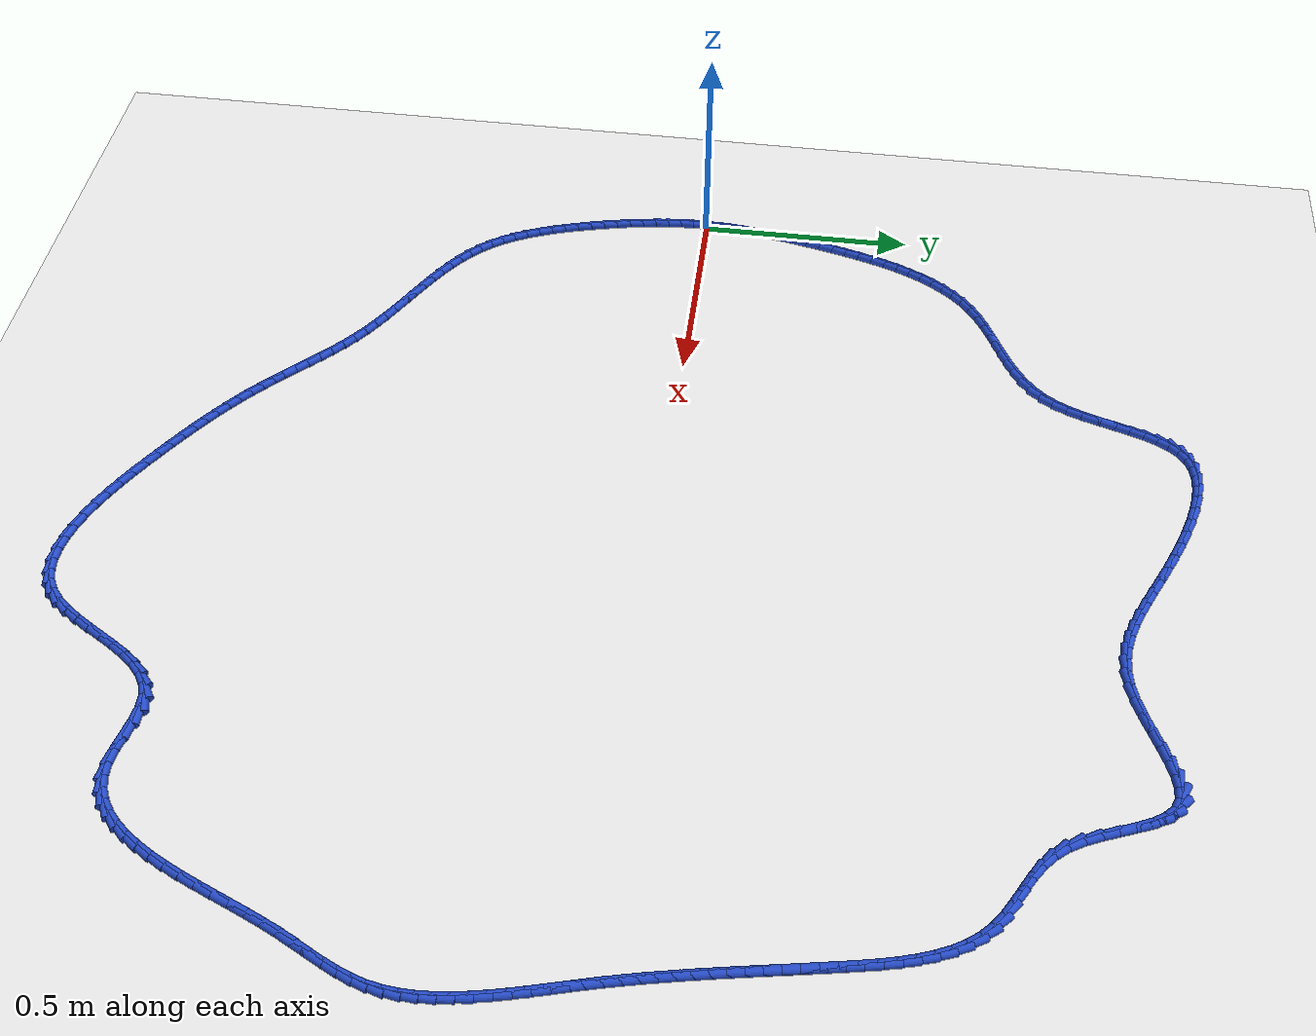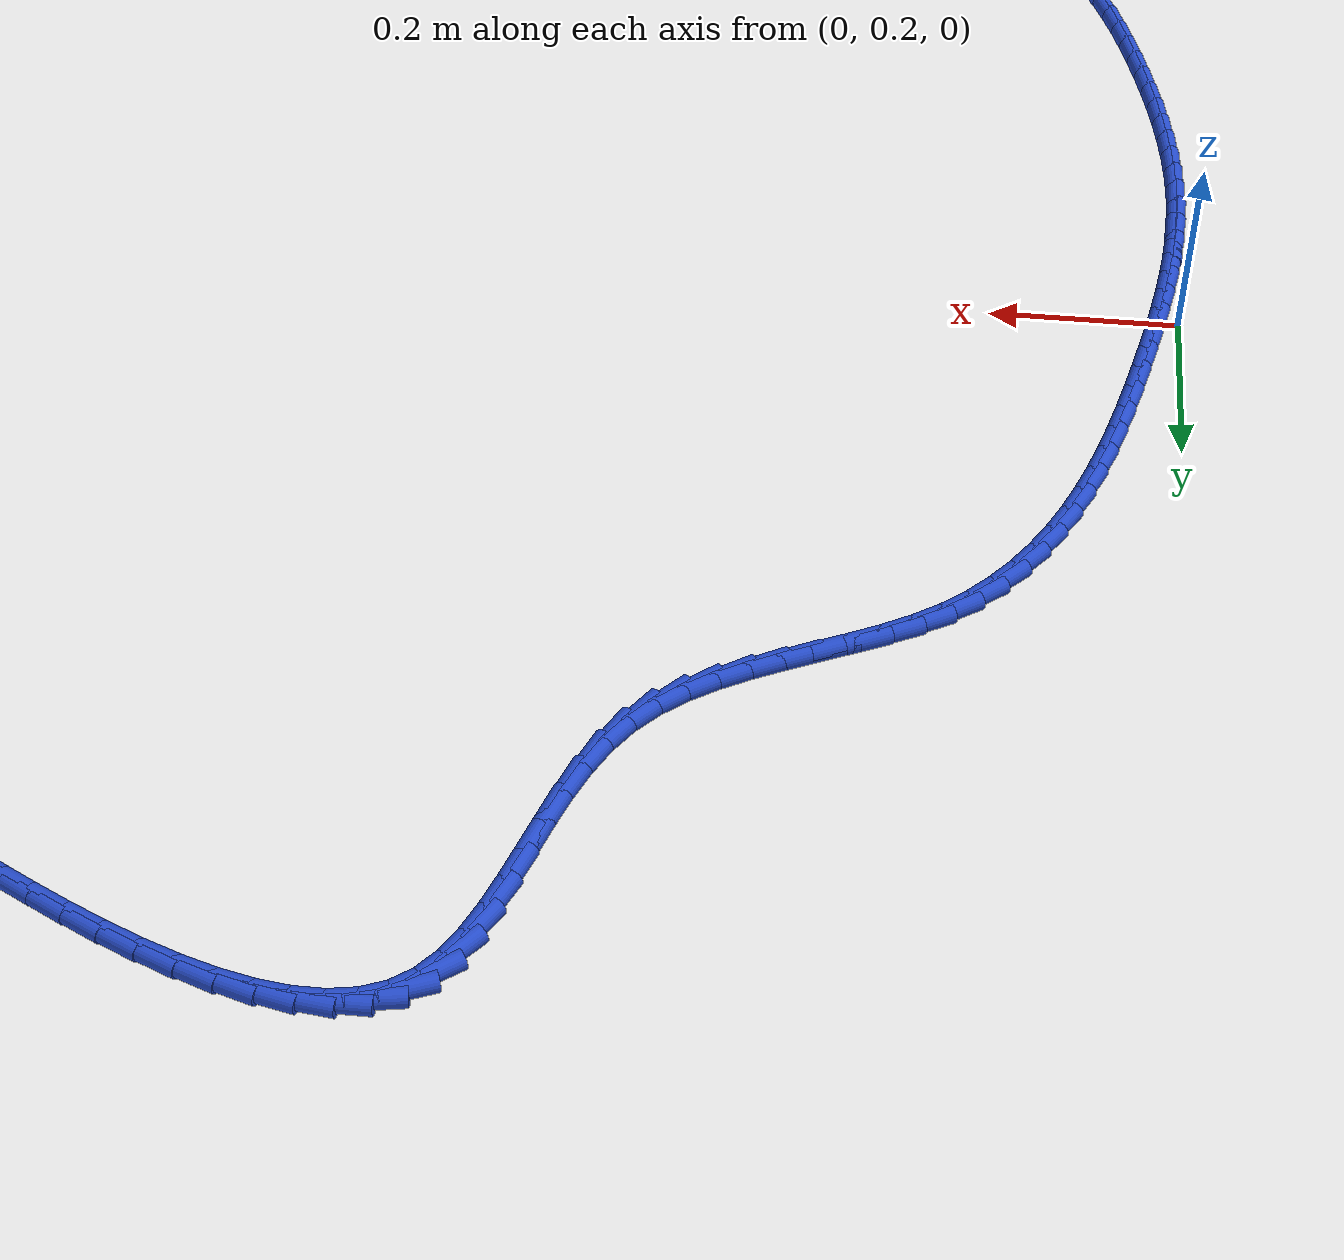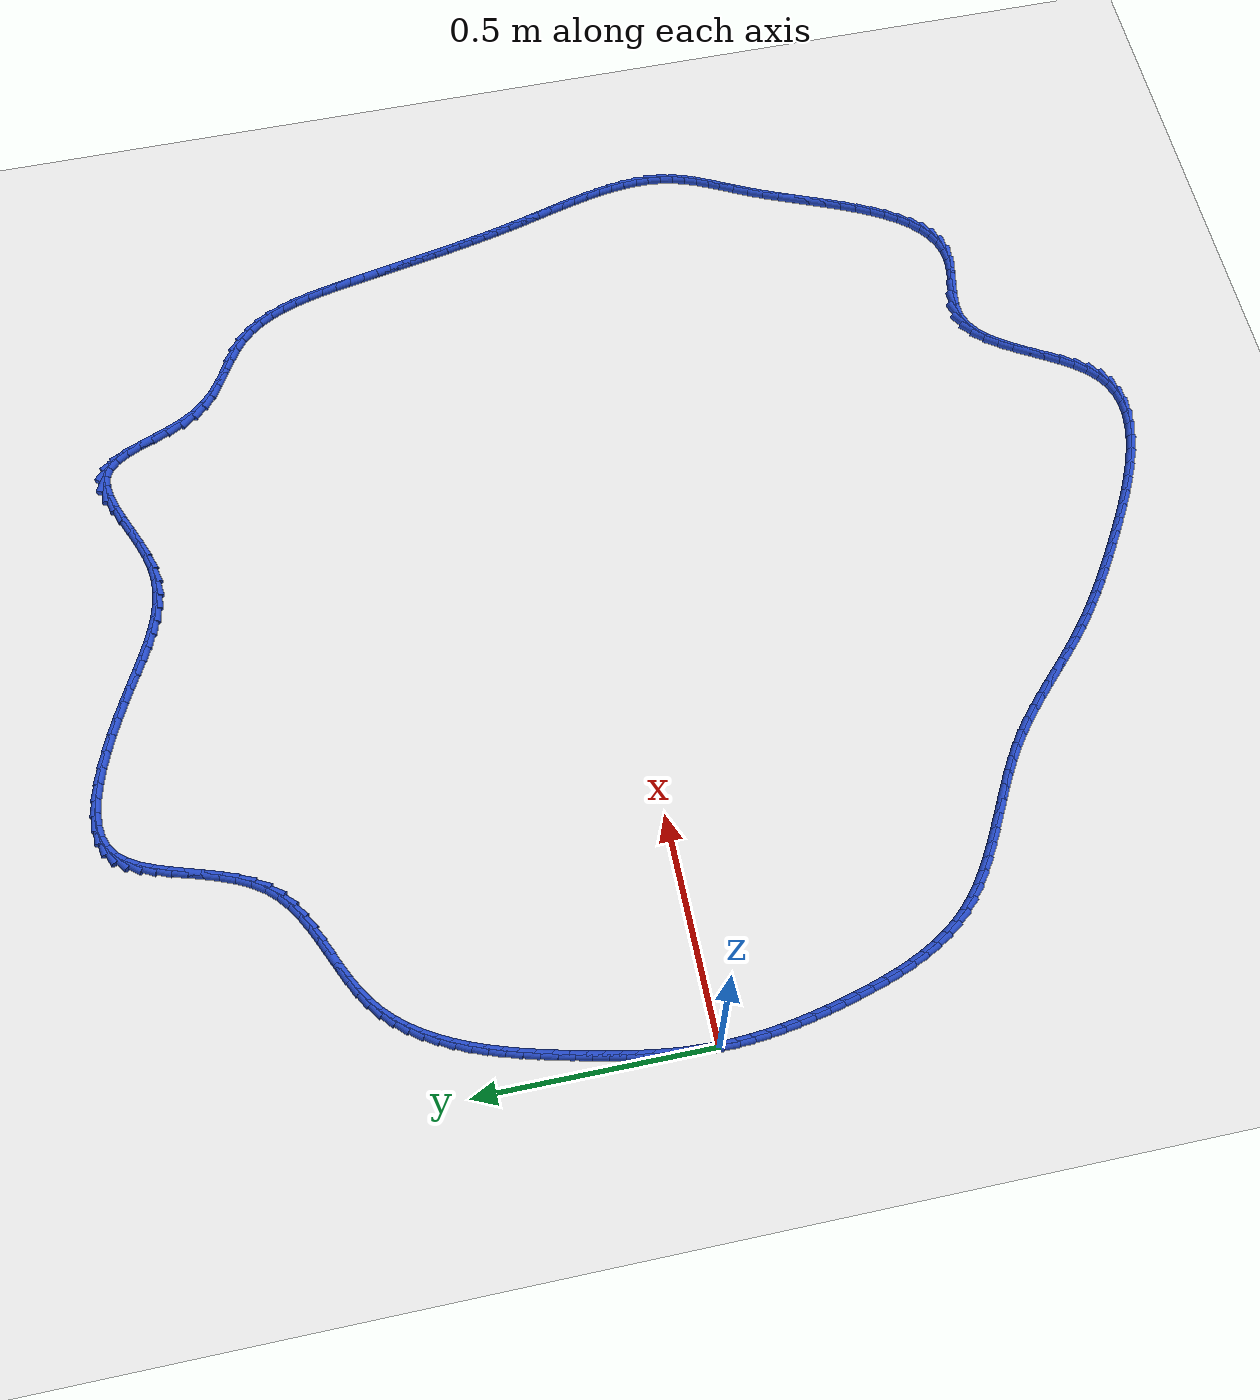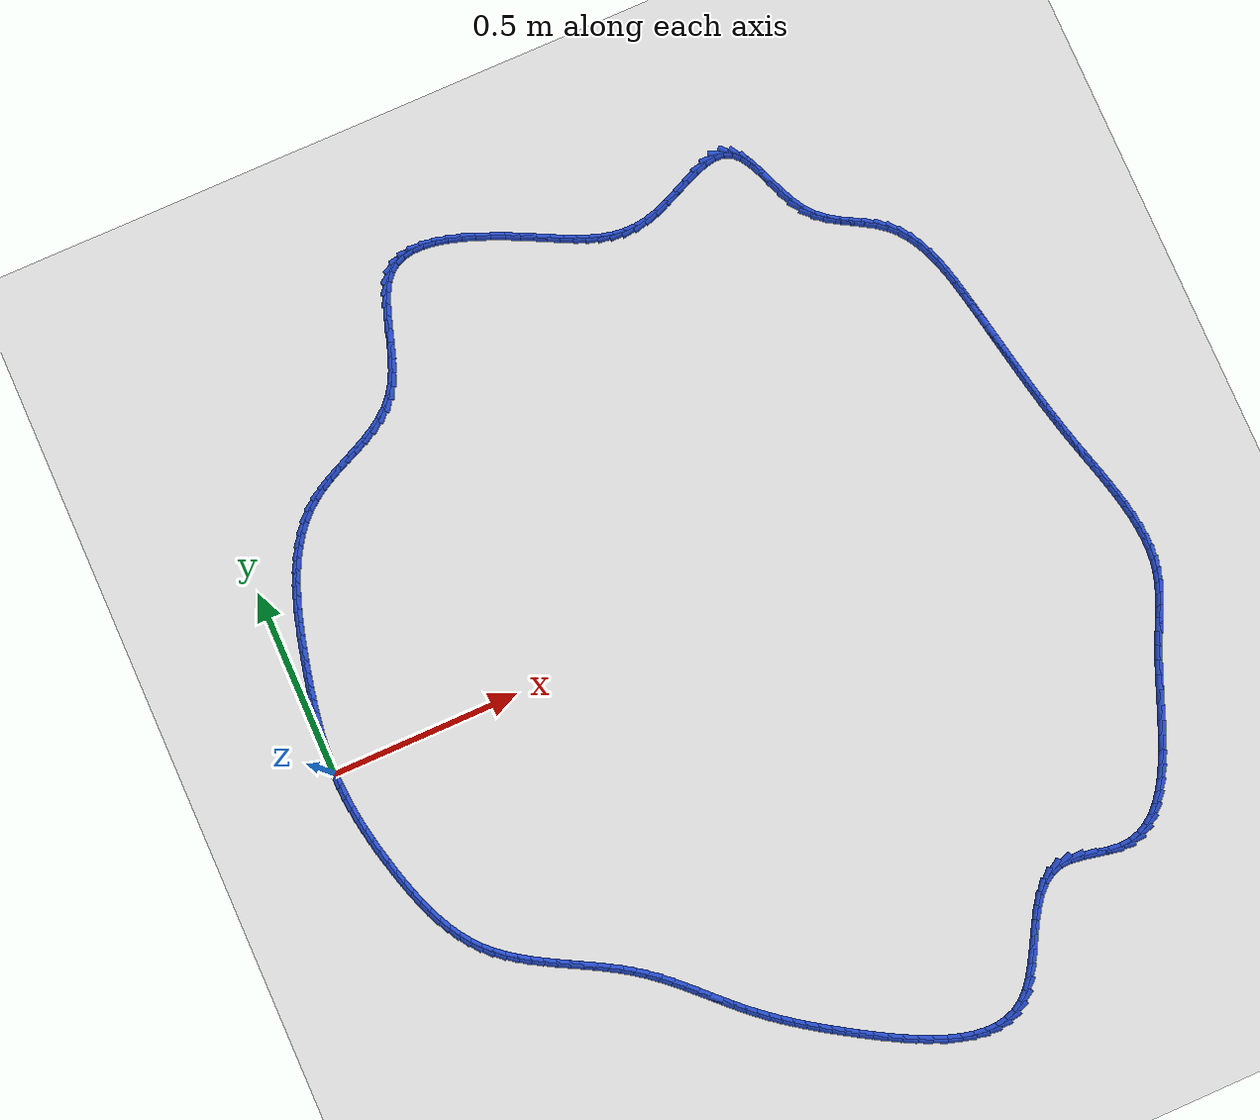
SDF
<sdf version="1.6">
 <world name="default">
  <light name="sun" type="directional">
   <pose>0 0 10 0 -0 0</pose>
   <diffuse>0.8 0.8 0.8 1</diffuse>
   <specular>0.2 0.2 0.2 1</specular>
   <attenuation>
    <range>1000</range>
    <constant>0.9</constant>
    <linear>0.01</linear>
    <quadratic>0.001</quadratic>
   </attenuation>
   <direction>-0.5 0.1 -0.9</direction>
  </light>
  <model name="ground_plane">
   <static>1</static>
   <link name="link">
    <collision name="collision">
     <geometry><plane><normal>0 0 1</normal><size>100 100</size></plane></geometry>
     <surface><friction><ode><mu>100</mu><mu2>50</mu2></ode></friction></surface>
    </collision>
    <visual name="visual">
     <cast_shadows>0</cast_shadows>
     <geometry><plane><normal>0 0 1</normal><size>100 100</size></plane></geometry>
     <material>
      <script><uri>file://media/materials/scripts/gazebo.material</uri><name>Gazebo/WhiteGlow</name></script>
     </material>
    </visual>
   </link>
  </model>
  <gravity>0 0 -9.8</gravity>
  <magnetic_field>6e-06 2.3e-05 -4.2e-05</magnetic_field>
  <atmosphere type="adiabatic"/>
  <physics name="default_physics" default="0" type="ode">
   <max_step_size>0.001</max_step_size>
   <real_time_factor>1</real_time_factor>
   <real_time_update_rate>1000</real_time_update_rate>
  </physics>
  <scene><ambient>0.4 0.4 0.4 1</ambient><background>0.7 0.7 0.7 1</background><shadows>1</shadows></scene>
  <spherical_coordinates>
   <surface_model>EARTH_WGS84</surface_model>
   <latitude_deg>0</latitude_deg>
   <longitude_deg>0</longitude_deg>
   <elevation>0</elevation>
   <heading_deg>0</heading_deg>
  </spherical_coordinates>
  <model name="line">
   <link name="link_0">
    <pose>-7.806255641895632e-18 -1.3877787807814457e-17 0.01 0 1.57 1.543758668066532</pose>
    <collision name="collision">
     <geometry><cylinder><radius>0.01</radius><length>0.08</length></cylinder></geometry>
    </collision>
    <visual name="visual">
     <material>
      <script><name>Gazebo/Blue</name><uri>file://media/materials/scripts/gazebo.material</uri></script>
     </material>
     <geometry><cylinder><radius>0.01</radius><length>0.08</length></cylinder></geometry>
    </visual>
   </link>
   <link name="link_1">
    <pose>0.0008558965189084472 0.0316480045075554 0.01 0 1.57 1.505740795909924</pose>
    <collision name="collision">
     <geometry><cylinder><radius>0.01</radius><length>0.08</length></cylinder></geometry>
    </collision>
    <visual name="visual">
     <material>
      <script><name>Gazebo/Blue</name><uri>file://media/materials/scripts/gazebo.material</uri></script>
     </material>
     <geometry><cylinder><radius>0.01</radius><length>0.08</length></cylinder></geometry>
    </visual>
   </link>
   <link name="link_2">
    <pose>0.0029159362944309 0.06326918636988166 0.01 0 1.57 1.471400113362632</pose>
    <collision name="collision">
     <geometry><cylinder><radius>0.01</radius><length>0.08</length></cylinder></geometry>
    </collision>
    <visual name="visual">
     <material>
      <script><name>Gazebo/Blue</name><uri>file://media/materials/scripts/gazebo.material</uri></script>
     </material>
     <geometry><cylinder><radius>0.01</radius><length>0.08</length></cylinder></geometry>
    </visual>
   </link>
   <link name="link_3">
    <pose>0.00607141226410911 0.09491101043141258 0.01 0 1.57 1.4409038023674445</pose>
    <collision name="collision">
     <geometry><cylinder><radius>0.01</radius><length>0.08</length></cylinder></geometry>
    </collision>
    <visual name="visual">
     <material>
      <script><name>Gazebo/Blue</name><uri>file://media/materials/scripts/gazebo.material</uri></script>
     </material>
     <geometry><cylinder><radius>0.01</radius><length>0.08</length></cylinder></geometry>
    </visual>
   </link>
   <link name="link_4">
    <pose>0.010213617365484838 0.12662094153658193 0.01 0 1.57 1.414343208902342</pose>
    <collision name="collision">
     <geometry><cylinder><radius>0.01</radius><length>0.08</length></cylinder></geometry>
    </collision>
    <visual name="visual">
     <material>
      <script><name>Gazebo/Blue</name><uri>file://media/materials/scripts/gazebo.material</uri></script>
     </material>
     <geometry><cylinder><radius>0.01</radius><length>0.08</length></cylinder></geometry>
    </visual>
   </link>
   <link name="link_5">
    <pose>0.015233844536099848 0.15844644452982354 0.01 0 1.57 1.3917465496848271</pose>
    <collision name="collision">
     <geometry><cylinder><radius>0.01</radius><length>0.08</length></cylinder></geometry>
    </collision>
    <visual name="visual">
     <material>
      <script><name>Gazebo/Blue</name><uri>file://media/materials/scripts/gazebo.material</uri></script>
     </material>
     <geometry><cylinder><radius>0.01</radius><length>0.08</length></cylinder></geometry>
    </visual>
   </link>
   <link name="link_6">
    <pose>0.02102338671349588 0.19043498425557104 0.01 0 1.57 1.3730919539369864</pose>
    <collision name="collision">
     <geometry><cylinder><radius>0.01</radius><length>0.08</length></cylinder></geometry>
    </collision>
    <visual name="visual">
     <material>
      <script><name>Gazebo/Blue</name><uri>file://media/materials/scripts/gazebo.material</uri></script>
     </material>
     <geometry><cylinder><radius>0.01</radius><length>0.08</length></cylinder></geometry>
    </visual>
   </link>
   <link name="link_7">
    <pose>0.02747353683521471 0.22263402555825837 0.01 0 1.57 1.3583195594884623</pose>
    <collision name="collision">
     <geometry><cylinder><radius>0.01</radius><length>0.08</length></cylinder></geometry>
    </collision>
    <visual name="visual">
     <material>
      <script><name>Gazebo/Blue</name><uri>file://media/materials/scripts/gazebo.material</uri></script>
     </material>
     <geometry><cylinder><radius>0.01</radius><length>0.08</length></cylinder></geometry>
    </visual>
   </link>
   <link name="link_8">
    <pose>0.034475587838798116 0.25509103328231936 0.01 0 1.57 1.3473319732001865</pose>
    <collision name="collision">
     <geometry><cylinder><radius>0.01</radius><length>0.08</length></cylinder></geometry>
    </collision>
    <visual name="visual">
     <material>
      <script><name>Gazebo/Blue</name><uri>file://media/materials/scripts/gazebo.material</uri></script>
     </material>
     <geometry><cylinder><radius>0.01</radius><length>0.08</length></cylinder></geometry>
    </visual>
   </link>
   <link name="link_9">
    <pose>0.04192111137246802 0.2878531935465328 0.01 0 1.57 1.3375063963695724</pose>
    <collision name="collision">
     <geometry><cylinder><radius>0.01</radius><length>0.08</length></cylinder></geometry>
    </collision>
    <visual name="visual">
     <material>
      <script><name>Gazebo/Blue</name><uri>file://media/materials/scripts/gazebo.material</uri></script>
     </material>
     <geometry><cylinder><radius>0.01</radius><length>0.08</length></cylinder></geometry>
    </visual>
   </link>
   <link name="link_10">
    <pose>0.04977276539147243 0.3208966023432861 0.01 0 1.57 1.3229385455392462</pose>
    <collision name="collision">
     <geometry><cylinder><radius>0.01</radius><length>0.08</length></cylinder></geometry>
    </collision>
    <visual name="visual">
     <material>
      <script><name>Gazebo/Blue</name><uri>file://media/materials/scripts/gazebo.material</uri></script>
     </material>
     <geometry><cylinder><radius>0.01</radius><length>0.08</length></cylinder></geometry>
    </visual>
   </link>
   <link name="link_11">
    <pose>0.058158153008186754 0.35403240164557254 0.01 0 1.57 1.3026931092101863</pose>
    <collision name="collision">
     <geometry><cylinder><radius>0.01</radius><length>0.08</length></cylinder></geometry>
    </collision>
    <visual name="visual">
     <material>
      <script><name>Gazebo/Blue</name><uri>file://media/materials/scripts/gazebo.material</uri></script>
     </material>
     <geometry><cylinder><radius>0.01</radius><length>0.08</length></cylinder></geometry>
    </visual>
   </link>
   <link name="link_12">
    <pose>0.06722821271247166 0.3870483967951238 0.01 0 1.57 1.276521718573467</pose>
    <collision name="collision">
     <geometry><cylinder><radius>0.01</radius><length>0.08</length></cylinder></geometry>
    </collision>
    <visual name="visual">
     <material>
      <script><name>Gazebo/Blue</name><uri>file://media/materials/scripts/gazebo.material</uri></script>
     </material>
     <geometry><cylinder><radius>0.01</radius><length>0.08</length></cylinder></geometry>
    </visual>
   </link>
   <link name="link_13">
    <pose>0.07713388299418776 0.41973239313367117 0.01 0 1.57 1.2440430461393286</pose>
    <collision name="collision">
     <geometry><cylinder><radius>0.01</radius><length>0.08</length></cylinder></geometry>
    </collision>
    <visual name="visual">
     <material>
      <script><name>Gazebo/Blue</name><uri>file://media/materials/scripts/gazebo.material</uri></script>
     </material>
     <geometry><cylinder><radius>0.01</radius><length>0.08</length></cylinder></geometry>
    </visual>
   </link>
   <link name="link_14">
    <pose>0.08802610234319569 0.4518721960029466 0.01 0 1.57 1.2047565377561085</pose>
    <collision name="collision">
     <geometry><cylinder><radius>0.01</radius><length>0.08</length></cylinder></geometry>
    </collision>
    <visual name="visual">
     <material>
      <script><name>Gazebo/Blue</name><uri>file://media/materials/scripts/gazebo.material</uri></script>
     </material>
     <geometry><cylinder><radius>0.01</radius><length>0.08</length></cylinder></geometry>
    </visual>
   </link>
   <link name="link_15">
    <pose>0.1000558092493561 0.4832556107446815 0.01 0 1.57 1.1580645969727832</pose>
    <collision name="collision">
     <geometry><cylinder><radius>0.01</radius><length>0.08</length></cylinder></geometry>
    </collision>
    <visual name="visual">
     <material>
      <script><name>Gazebo/Blue</name><uri>file://media/materials/scripts/gazebo.material</uri></script>
     </material>
     <geometry><cylinder><radius>0.01</radius><length>0.08</length></cylinder></geometry>
    </visual>
   </link>
   <link name="link_16">
    <pose>0.11337394220252965 0.5136704427006076 0.01 0 1.57 1.1033120941979375</pose>
    <collision name="collision">
     <geometry><cylinder><radius>0.01</radius><length>0.08</length></cylinder></geometry>
    </collision>
    <visual name="visual">
     <material>
      <script><name>Gazebo/Blue</name><uri>file://media/materials/scripts/gazebo.material</uri></script>
     </material>
     <geometry><cylinder><radius>0.01</radius><length>0.08</length></cylinder></geometry>
    </visual>
   </link>
   <link name="link_17">
    <pose>0.12813143969257695 0.5429044972124563 0.01 0 1.57 1.039854661652886</pose>
    <collision name="collision">
     <geometry><cylinder><radius>0.01</radius><length>0.08</length></cylinder></geometry>
    </collision>
    <visual name="visual">
     <material>
      <script><name>Gazebo/Blue</name><uri>file://media/materials/scripts/gazebo.material</uri></script>
     </material>
     <geometry><cylinder><radius>0.01</radius><length>0.08</length></cylinder></geometry>
    </visual>
   </link>
   <link name="link_18">
    <pose>0.1444792402093586 0.5707455796219593 0.01 0 1.57 0.9671682220580119</pose>
    <collision name="collision">
     <geometry><cylinder><radius>0.01</radius><length>0.08</length></cylinder></geometry>
    </collision>
    <visual name="visual">
     <material>
      <script><name>Gazebo/Blue</name><uri>file://media/materials/scripts/gazebo.material</uri></script>
     </material>
     <geometry><cylinder><radius>0.01</radius><length>0.08</length></cylinder></geometry>
    </visual>
   </link>
   <link name="link_19">
    <pose>0.16256828224273534 0.5969814952708483 0.01 0 1.57 0.8850078232531806</pose>
    <collision name="collision">
     <geometry><cylinder><radius>0.01</radius><length>0.08</length></cylinder></geometry>
    </collision>
    <visual name="visual">
     <material>
      <script><name>Gazebo/Blue</name><uri>file://media/materials/scripts/gazebo.material</uri></script>
     </material>
     <geometry><cylinder><radius>0.01</radius><length>0.08</length></cylinder></geometry>
    </visual>
   </link>
   <link name="link_20">
    <pose>0.18254950428256778 0.6214000495008549 0.01 0 1.57 0.7936085216722211</pose>
    <collision name="collision">
     <geometry><cylinder><radius>0.01</radius><length>0.08</length></cylinder></geometry>
    </collision>
    <visual name="visual">
     <material>
      <script><name>Gazebo/Blue</name><uri>file://media/materials/scripts/gazebo.material</uri></script>
     </material>
     <geometry><cylinder><radius>0.01</radius><length>0.08</length></cylinder></geometry>
    </visual>
   </link>
   <link name="link_21">
    <pose>0.20457384481871638 0.6437890476537105 0.01 0 1.57 0.6938908633965613</pose>
    <collision name="collision">
     <geometry><cylinder><radius>0.01</radius><length>0.08</length></cylinder></geometry>
    </collision>
    <visual name="visual">
     <material>
      <script><name>Gazebo/Blue</name><uri>file://media/materials/scripts/gazebo.material</uri></script>
     </material>
     <geometry><cylinder><radius>0.01</radius><length>0.08</length></cylinder></geometry>
    </visual>
   </link>
   <link name="link_22">
    <pose>0.22879224234104195 0.6639362950711466 0.01 0 1.57 0.5924047732687826</pose>
    <collision name="collision">
     <geometry><cylinder><radius>0.01</radius><length>0.08</length></cylinder></geometry>
    </collision>
    <visual name="visual">
     <material>
      <script><name>Gazebo/Blue</name><uri>file://media/materials/scripts/gazebo.material</uri></script>
     </material>
     <geometry><cylinder><radius>0.01</radius><length>0.08</length></cylinder></geometry>
    </visual>
   </link>
   <link name="link_23">
    <pose>0.2552536741422328 0.6817460059893444 0.01 0 1.57 0.5133283043003264</pose>
    <collision name="collision">
     <geometry><cylinder><radius>0.01</radius><length>0.08</length></cylinder></geometry>
    </collision>
    <visual name="visual">
     <material>
      <script><name>Gazebo/Blue</name><uri>file://media/materials/scripts/gazebo.material</uri></script>
     </material>
     <geometry><cylinder><radius>0.01</radius><length>0.08</length></cylinder></geometry>
    </visual>
   </link>
   <link name="link_24">
    <pose>0.283518691610286 0.697680029520909 0.01 0 1.57 0.46216572186184385</pose>
    <collision name="collision">
     <geometry><cylinder><radius>0.01</radius><length>0.08</length></cylinder></geometry>
    </collision>
    <visual name="visual">
     <material>
      <script><name>Gazebo/Blue</name><uri>file://media/materials/scripts/gazebo.material</uri></script>
     </material>
     <geometry><cylinder><radius>0.01</radius><length>0.08</length></cylinder></geometry>
    </visual>
   </link>
   <link name="link_25">
    <pose>0.3130017661820029 0.7123669939659347 0.01 0 1.57 0.4370259539608368</pose>
    <collision name="collision">
     <geometry><cylinder><radius>0.01</radius><length>0.08</length></cylinder></geometry>
    </collision>
    <visual name="visual">
     <material>
      <script><name>Gazebo/Blue</name><uri>file://media/materials/scripts/gazebo.material</uri></script>
     </material>
     <geometry><cylinder><radius>0.01</radius><length>0.08</length></cylinder></geometry>
    </visual>
   </link>
   <link name="link_26">
    <pose>0.343117342812616 0.7264355578584716 0.01 0 1.57 0.4367082186893146</pose>
    <collision name="collision">
     <geometry><cylinder><radius>0.01</radius><length>0.08</length></cylinder></geometry>
    </collision>
    <visual name="visual">
     <material>
      <script><name>Gazebo/Blue</name><uri>file://media/materials/scripts/gazebo.material</uri></script>
     </material>
     <geometry><cylinder><radius>0.01</radius><length>0.08</length></cylinder></geometry>
    </visual>
   </link>
   <link name="link_27">
    <pose>0.37327986645735733 0.7405143797325687 0.01 0 1.57 0.46109995841185386</pose>
    <collision name="collision">
     <geometry><cylinder><radius>0.01</radius><length>0.08</length></cylinder></geometry>
    </collision>
    <visual name="visual">
     <material>
      <script><name>Gazebo/Blue</name><uri>file://media/materials/scripts/gazebo.material</uri></script>
     </material>
     <geometry><cylinder><radius>0.01</radius><length>0.08</length></cylinder></geometry>
    </visual>
   </link>
   <link name="link_28">
    <pose>0.4029037820714588 0.7552321181222753 0.01 0 1.57 0.5111679207233936</pose>
    <collision name="collision">
     <geometry><cylinder><radius>0.01</radius><length>0.08</length></cylinder></geometry>
    </collision>
    <visual name="visual">
     <material>
      <script><name>Gazebo/Blue</name><uri>file://media/materials/scripts/gazebo.material</uri></script>
     </material>
     <geometry><cylinder><radius>0.01</radius><length>0.08</length></cylinder></geometry>
    </visual>
   </link>
   <link name="link_29">
    <pose>0.431403534610153 0.7712174315616412 0.01 0 1.57 0.5885586222143333</pose>
    <collision name="collision">
     <geometry><cylinder><radius>0.01</radius><length>0.08</length></cylinder></geometry>
    </collision>
    <visual name="visual">
     <material>
      <script><name>Gazebo/Blue</name><uri>file://media/materials/scripts/gazebo.material</uri></script>
     </material>
     <geometry><cylinder><radius>0.01</radius><length>0.08</length></cylinder></geometry>
    </visual>
   </link>
   <link name="link_30">
    <pose>0.4581935690286717 0.7890989785847154 0.01 0 1.57 0.6945970259362806</pose>
    <collision name="collision">
     <geometry><cylinder><radius>0.01</radius><length>0.08</length></cylinder></geometry>
    </collision>
    <visual name="visual">
     <material>
      <script><name>Gazebo/Blue</name><uri>file://media/materials/scripts/gazebo.material</uri></script>
     </material>
     <geometry><cylinder><radius>0.01</radius><length>0.08</length></cylinder></geometry>
    </visual>
   </link>
   <link name="link_31">
    <pose>0.48268833028224717 0.8095054177255475 0.01 0 1.57 0.8284507504421147</pose>
    <collision name="collision">
     <geometry><cylinder><radius>0.01</radius><length>0.08</length></cylinder></geometry>
    </collision>
    <visual name="visual">
     <material>
      <script><name>Gazebo/Blue</name><uri>file://media/materials/scripts/gazebo.material</uri></script>
     </material>
     <geometry><cylinder><radius>0.01</radius><length>0.08</length></cylinder></geometry>
    </visual>
   </link>
   <link name="link_32">
    <pose>0.5043022633261116 0.8330654075181869 0.01 0 1.57 0.9795465984308942</pose>
    <collision name="collision">
     <geometry><cylinder><radius>0.01</radius><length>0.08</length></cylinder></geometry>
    </collision>
    <visual name="visual">
     <material>
      <script><name>Gazebo/Blue</name><uri>file://media/materials/scripts/gazebo.material</uri></script>
     </material>
     <geometry><cylinder><radius>0.01</radius><length>0.08</length></cylinder></geometry>
    </visual>
   </link>
   <link name="link_33">
    <pose>0.5225648713107278 0.8602675248480662 0.01 0 1.57 1.1044709969895836</pose>
    <collision name="collision">
     <geometry><cylinder><radius>0.01</radius><length>0.08</length></cylinder></geometry>
    </collision>
    <visual name="visual">
     <material>
      <script><name>Gazebo/Blue</name><uri>file://media/materials/scripts/gazebo.material</uri></script>
     </material>
     <geometry><cylinder><radius>0.01</radius><length>0.08</length></cylinder></geometry>
    </visual>
   </link>
   <link name="link_34">
    <pose>0.5378306959653324 0.8905958743502436 0.01 0 1.57 1.190725432326556</pose>
    <collision name="collision">
     <geometry><cylinder><radius>0.01</radius><length>0.08</length></cylinder></geometry>
    </collision>
    <visual name="visual">
     <material>
      <script><name>Gazebo/Blue</name><uri>file://media/materials/scripts/gazebo.material</uri></script>
     </material>
     <geometry><cylinder><radius>0.01</radius><length>0.08</length></cylinder></geometry>
    </visual>
   </link>
   <link name="link_35">
    <pose>0.5508143856995672 0.9230961361097657 0.01 0 1.57 1.2442744921775082</pose>
    <collision name="collision">
     <geometry><cylinder><radius>0.01</radius><length>0.08</length></cylinder></geometry>
    </collision>
    <visual name="visual">
     <material>
      <script><name>Gazebo/Blue</name><uri>file://media/materials/scripts/gazebo.material</uri></script>
     </material>
     <geometry><cylinder><radius>0.01</radius><length>0.08</length></cylinder></geometry>
    </visual>
   </link>
   <link name="link_36">
    <pose>0.5622320901503481 0.9568121624897081 0.01 0 1.57 1.2692398446456856</pose>
    <collision name="collision">
     <geometry><cylinder><radius>0.01</radius><length>0.08</length></cylinder></geometry>
    </collision>
    <visual name="visual">
     <material>
      <script><name>Gazebo/Blue</name><uri>file://media/materials/scripts/gazebo.material</uri></script>
     </material>
     <geometry><cylinder><radius>0.01</radius><length>0.08</length></cylinder></geometry>
    </visual>
   </link>
   <link name="link_37">
    <pose>0.572799958954591 0.9907878058531462 0.01 0 1.57 1.266968375332468</pose>
    <collision name="collision">
     <geometry><cylinder><radius>0.01</radius><length>0.08</length></cylinder></geometry>
    </collision>
    <visual name="visual">
     <material>
      <script><name>Gazebo/Blue</name><uri>file://media/materials/scripts/gazebo.material</uri></script>
     </material>
     <geometry><cylinder><radius>0.01</radius><length>0.08</length></cylinder></geometry>
    </visual>
   </link>
   <link name="link_38">
    <pose>0.5832341417492113 1.0240669185631541 0.01 0 1.57 1.2356040957616927</pose>
    <collision name="collision">
     <geometry><cylinder><radius>0.01</radius><length>0.08</length></cylinder></geometry>
    </collision>
    <visual name="visual">
     <material>
      <script><name>Gazebo/Blue</name><uri>file://media/materials/scripts/gazebo.material</uri></script>
     </material>
     <geometry><cylinder><radius>0.01</radius><length>0.08</length></cylinder></geometry>
    </visual>
   </link>
   <link name="link_39">
    <pose>0.5942507881711245 1.055693352982808 0.01 0 1.57 1.1694285441774839</pose>
    <collision name="collision">
     <geometry><cylinder><radius>0.01</radius><length>0.08</length></cylinder></geometry>
    </collision>
    <visual name="visual">
     <material>
      <script><name>Gazebo/Blue</name><uri>file://media/materials/scripts/gazebo.material</uri></script>
     </material>
     <geometry><cylinder><radius>0.01</radius><length>0.08</length></cylinder></geometry>
    </visual>
   </link>
   <link name="link_40">
    <pose>0.6065660478572467 1.0847109614751818 0.01 0 1.57 1.0580214836642494</pose>
    <collision name="collision">
     <geometry><cylinder><radius>0.01</radius><length>0.08</length></cylinder></geometry>
    </collision>
    <visual name="visual">
     <material>
      <script><name>Gazebo/Blue</name><uri>file://media/materials/scripts/gazebo.material</uri></script>
     </material>
     <geometry><cylinder><radius>0.01</radius><length>0.08</length></cylinder></geometry>
    </visual>
   </link>
   <link name="link_41">
    <pose>0.6208960704444932 1.1101635964033512 0.01 0 1.57 0.8869254545343136</pose>
    <collision name="collision">
     <geometry><cylinder><radius>0.01</radius><length>0.08</length></cylinder></geometry>
    </collision>
    <visual name="visual">
     <material>
      <script><name>Gazebo/Blue</name><uri>file://media/materials/scripts/gazebo.material</uri></script>
     </material>
     <geometry><cylinder><radius>0.01</radius><length>0.08</length></cylinder></geometry>
    </visual>
   </link>
   <link name="link_42">
    <pose>0.6379570055697799 1.131095110130391 0.01 0 1.57 0.6479128703624005</pose>
    <collision name="collision">
     <geometry><cylinder><radius>0.01</radius><length>0.08</length></cylinder></geometry>
    </collision>
    <visual name="visual">
     <material>
      <script><name>Gazebo/Blue</name><uri>file://media/materials/scripts/gazebo.material</uri></script>
     </material>
     <geometry><cylinder><radius>0.01</radius><length>0.08</length></cylinder></geometry>
    </visual>
   </link>
   <link name="link_43">
    <pose>0.6584311290847005 1.146592308093387 0.01 0 1.57 0.3923210060359048</pose>
    <collision name="collision">
     <geometry><cylinder><radius>0.01</radius><length>0.08</length></cylinder></geometry>
    </collision>
    <visual name="visual">
     <material>
      <script><name>Gazebo/Blue</name><uri>file://media/materials/scripts/gazebo.material</uri></script>
     </material>
     <geometry><cylinder><radius>0.01</radius><length>0.08</length></cylinder></geometry>
    </visual>
   </link>
   <link name="link_44">
    <pose>0.682396313557764 1.1565083989732312 0.01 0 1.57 0.17759906851085347</pose>
    <collision name="collision">
     <geometry><cylinder><radius>0.01</radius><length>0.08</length></cylinder></geometry>
    </collision>
    <visual name="visual">
     <material>
      <script><name>Gazebo/Blue</name><uri>file://media/materials/scripts/gazebo.material</uri></script>
     </material>
     <geometry><cylinder><radius>0.01</radius><length>0.08</length></cylinder></geometry>
    </visual>
   </link>
   <link name="link_45">
    <pose>0.7094096031333837 1.1613570190243616 0.01 0 1.57 0.010688148107674551</pose>
    <collision name="collision">
     <geometry><cylinder><radius>0.01</radius><length>0.08</length></cylinder></geometry>
    </collision>
    <visual name="visual">
     <material>
      <script><name>Gazebo/Blue</name><uri>file://media/materials/scripts/gazebo.material</uri></script>
     </material>
     <geometry><cylinder><radius>0.01</radius><length>0.08</length></cylinder></geometry>
    </visual>
   </link>
   <link name="link_46">
    <pose>0.7390109992770937 1.1616734151786288 0.01 0 1.57 -0.11548256608917344</pose>
    <collision name="collision">
     <geometry><cylinder><radius>0.01</radius><length>0.08</length></cylinder></geometry>
    </collision>
    <visual name="visual">
     <material>
      <script><name>Gazebo/Blue</name><uri>file://media/materials/scripts/gazebo.material</uri></script>
     </material>
     <geometry><cylinder><radius>0.01</radius><length>0.08</length></cylinder></geometry>
    </visual>
   </link>
   <link name="link_47">
    <pose>0.7707405034544269 1.1579928343678823 0.01 0 1.57 -0.2106833294217414</pose>
    <collision name="collision">
     <geometry><cylinder><radius>0.01</radius><length>0.08</length></cylinder></geometry>
    </collision>
    <visual name="visual">
     <material>
      <script><name>Gazebo/Blue</name><uri>file://media/materials/scripts/gazebo.material</uri></script>
     </material>
     <geometry><cylinder><radius>0.01</radius><length>0.08</length></cylinder></geometry>
    </visual>
   </link>
   <link name="link_48">
    <pose>0.8041381171309175 1.150850523523973 0.01 0 1.57 -0.2831403851998883</pose>
    <collision name="collision">
     <geometry><cylinder><radius>0.01</radius><length>0.08</length></cylinder></geometry>
    </collision>
    <visual name="visual">
     <material>
      <script><name>Gazebo/Blue</name><uri>file://media/materials/scripts/gazebo.material</uri></script>
     </material>
     <geometry><cylinder><radius>0.01</radius><length>0.08</length></cylinder></geometry>
    </visual>
   </link>
   <link name="link_49">
    <pose>0.8387438417720987 1.1407817295787506 0.01 0 1.57 -0.33884496505204237</pose>
    <collision name="collision">
     <geometry><cylinder><radius>0.01</radius><length>0.08</length></cylinder></geometry>
    </collision>
    <visual name="visual">
     <material>
      <script><name>Gazebo/Blue</name><uri>file://media/materials/scripts/gazebo.material</uri></script>
     </material>
     <geometry><cylinder><radius>0.01</radius><length>0.08</length></cylinder></geometry>
    </visual>
   </link>
   <link name="link_50">
    <pose>0.874097678843504 1.1283216994640655 0.01 0 1.57 -0.38193836346112814</pose>
    <collision name="collision">
     <geometry><cylinder><radius>0.01</radius><length>0.08</length></cylinder></geometry>
    </collision>
    <visual name="visual">
     <material>
      <script><name>Gazebo/Blue</name><uri>file://media/materials/scripts/gazebo.material</uri></script>
     </material>
     <geometry><cylinder><radius>0.01</radius><length>0.08</length></cylinder></geometry>
    </visual>
   </link>
   <link name="link_51">
    <pose>0.9097396298106672 1.114005680111768 0.01 0 1.57 -0.41521365847846736</pose>
    <collision name="collision">
     <geometry><cylinder><radius>0.01</radius><length>0.08</length></cylinder></geometry>
    </collision>
    <visual name="visual">
     <material>
      <script><name>Gazebo/Blue</name><uri>file://media/materials/scripts/gazebo.material</uri></script>
     </material>
     <geometry><cylinder><radius>0.01</radius><length>0.08</length></cylinder></geometry>
    </visual>
   </link>
   <link name="link_52">
    <pose>0.9452096961391216 1.0983689184537078 0.01 0 1.57 -0.44049610199473566</pose>
    <collision name="collision">
     <geometry><cylinder><radius>0.01</radius><length>0.08</length></cylinder></geometry>
    </collision>
    <visual name="visual">
     <material>
      <script><name>Gazebo/Blue</name><uri>file://media/materials/scripts/gazebo.material</uri></script>
     </material>
     <geometry><cylinder><radius>0.01</radius><length>0.08</length></cylinder></geometry>
    </visual>
   </link>
   <link name="link_53">
    <pose>0.9800478792944008 1.0819466614217355 0.01 0 1.57 -0.4588191028057761</pose>
    <collision name="collision">
     <geometry><cylinder><radius>0.01</radius><length>0.08</length></cylinder></geometry>
    </collision>
    <visual name="visual">
     <material>
      <script><name>Gazebo/Blue</name><uri>file://media/materials/scripts/gazebo.material</uri></script>
     </material>
     <geometry><cylinder><radius>0.01</radius><length>0.08</length></cylinder></geometry>
    </visual>
   </link>
   <link name="link_54">
    <pose>1.0137996651301913 1.0652739928319868 0.01 0 1.57 -0.4673045646895924</pose>
    <collision name="collision">
     <geometry><cylinder><radius>0.01</radius><length>0.08</length></cylinder></geometry>
    </collision>
    <visual name="visual">
     <material>
      <script><name>Gazebo/Blue</name><uri>file://media/materials/scripts/gazebo.material</uri></script>
     </material>
     <geometry><cylinder><radius>0.01</radius><length>0.08</length></cylinder></geometry>
    </visual>
   </link>
   <link name="link_55">
    <pose>1.0462949452497448 1.0488775377544979 0.01 0 1.57 -0.4601664658742699</pose>
    <collision name="collision">
     <geometry><cylinder><radius>0.01</radius><length>0.08</length></cylinder></geometry>
    </collision>
    <visual name="visual">
     <material>
      <script><name>Gazebo/Blue</name><uri>file://media/materials/scripts/gazebo.material</uri></script>
     </material>
     <geometry><cylinder><radius>0.01</radius><length>0.08</length></cylinder></geometry>
    </visual>
   </link>
   <link name="link_56">
    <pose>1.0777805167422847 1.033271521729199 0.01 0 1.57 -0.4352807061181367</pose>
    <collision name="collision">
     <geometry><cylinder><radius>0.01</radius><length>0.08</length></cylinder></geometry>
    </collision>
    <visual name="visual">
     <material>
      <script><name>Gazebo/Blue</name><uri>file://media/materials/scripts/gazebo.material</uri></script>
     </material>
     <geometry><cylinder><radius>0.01</radius><length>0.08</length></cylinder></geometry>
    </visual>
   </link>
   <link name="link_57">
    <pose>1.1085363821886196 1.0189691827040934 0.01 0 1.57 -0.3907880509113712</pose>
    <collision name="collision">
     <geometry><cylinder><radius>0.01</radius><length>0.08</length></cylinder></geometry>
    </collision>
    <visual name="visual">
     <material>
      <script><name>Gazebo/Blue</name><uri>file://media/materials/scripts/gazebo.material</uri></script>
     </material>
     <geometry><cylinder><radius>0.01</radius><length>0.08</length></cylinder></geometry>
    </visual>
   </link>
   <link name="link_58">
    <pose>1.1388425441695582 1.0064837586271835 0.01 0 1.57 -0.32502557453167613</pose>
    <collision name="collision">
     <geometry><cylinder><radius>0.01</radius><length>0.08</length></cylinder></geometry>
    </collision>
    <visual name="visual">
     <material>
      <script><name>Gazebo/Blue</name><uri>file://media/materials/scripts/gazebo.material</uri></script>
     </material>
     <geometry><cylinder><radius>0.01</radius><length>0.08</length></cylinder></geometry>
    </visual>
   </link>
   <link name="link_59">
    <pose>1.1689790052659095 0.9963284874464731 0.01 0 1.57 -0.23719043581093252</pose>
    <collision name="collision">
     <geometry><cylinder><radius>0.01</radius><length>0.08</length></cylinder></geometry>
    </collision>
    <visual name="visual">
     <material>
      <script><name>Gazebo/Blue</name><uri>file://media/materials/scripts/gazebo.material</uri></script>
     </material>
     <geometry><cylinder><radius>0.01</radius><length>0.08</length></cylinder></geometry>
    </visual>
   </link>
   <link name="link_60">
    <pose>1.1992257680584817 0.9890166071099648 0.01 0 1.57 -0.12839005825136435</pose>
    <collision name="collision">
     <geometry><cylinder><radius>0.01</radius><length>0.08</length></cylinder></geometry>
    </collision>
    <visual name="visual">
     <material>
      <script><name>Gazebo/Blue</name><uri>file://media/materials/scripts/gazebo.material</uri></script>
     </material>
     <geometry><cylinder><radius>0.01</radius><length>0.08</length></cylinder></geometry>
    </visual>
   </link>
   <link name="link_61">
    <pose>1.2298628351280843 0.9850613555656613 0.01 0 1.57 -0.0027272997279025797</pose>
    <collision name="collision">
     <geometry><cylinder><radius>0.01</radius><length>0.08</length></cylinder></geometry>
    </collision>
    <visual name="visual">
     <material>
      <script><name>Gazebo/Blue</name><uri>file://media/materials/scripts/gazebo.material</uri></script>
     </material>
     <geometry><cylinder><radius>0.01</radius><length>0.08</length></cylinder></geometry>
    </visual>
   </link>
   <link name="link_62">
    <pose>1.261170209055525 0.9849759707615655 0.01 0 1.57 0.1324508776225954</pose>
    <collision name="collision">
     <geometry><cylinder><radius>0.01</radius><length>0.08</length></cylinder></geometry>
    </collision>
    <visual name="visual">
     <material>
      <script><name>Gazebo/Blue</name><uri>file://media/materials/scripts/gazebo.material</uri></script>
     </material>
     <geometry><cylinder><radius>0.01</radius><length>0.08</length></cylinder></geometry>
    </visual>
   </link>
   <link name="link_63">
    <pose>1.2934278924216134 0.9892736906456812 0.01 0 1.57 0.26433159499002545</pose>
    <collision name="collision">
     <geometry><cylinder><radius>0.01</radius><length>0.08</length></cylinder></geometry>
    </collision>
    <visual name="visual">
     <material>
      <script><name>Gazebo/Blue</name><uri>file://media/materials/scripts/gazebo.material</uri></script>
     </material>
     <geometry><cylinder><radius>0.01</radius><length>0.08</length></cylinder></geometry>
    </visual>
   </link>
   <link name="link_64">
    <pose>1.3268551706488958 0.9983212866600673 0.01 0 1.57 0.3577117290123947</pose>
    <collision name="collision">
     <geometry><cylinder><radius>0.01</radius><length>0.08</length></cylinder></geometry>
    </collision>
    <visual name="visual">
     <material>
      <script><name>Gazebo/Blue</name><uri>file://media/materials/scripts/gazebo.material</uri></script>
     </material>
     <geometry><cylinder><radius>0.01</radius><length>0.08</length></cylinder></geometry>
    </visual>
   </link>
   <link name="link_65">
    <pose>1.3611070760004595 1.011124396242834 0.01 0 1.57 0.4066435163237283</pose>
    <collision name="collision">
     <geometry><cylinder><radius>0.01</radius><length>0.08</length></cylinder></geometry>
    </collision>
    <visual name="visual">
     <material>
      <script><name>Gazebo/Blue</name><uri>file://media/materials/scripts/gazebo.material</uri></script>
     </material>
     <geometry><cylinder><radius>0.01</radius><length>0.08</length></cylinder></geometry>
    </visual>
   </link>
   <link name="link_66">
    <pose>1.395532208485417 1.0259494578505726 0.01 0 1.57 0.4187142075795374</pose>
    <collision name="collision">
     <geometry><cylinder><radius>0.01</radius><length>0.08</length></cylinder></geometry>
    </collision>
    <visual name="visual">
     <material>
      <script><name>Gazebo/Blue</name><uri>file://media/materials/scripts/gazebo.material</uri></script>
     </material>
     <geometry><cylinder><radius>0.01</radius><length>0.08</length></cylinder></geometry>
    </visual>
   </link>
   <link name="link_67">
    <pose>1.4294761205208637 1.041055558308686 0.01 0 1.57 0.39417088214150325</pose>
    <collision name="collision">
     <geometry><cylinder><radius>0.01</radius><length>0.08</length></cylinder></geometry>
    </collision>
    <visual name="visual">
     <material>
      <script><name>Gazebo/Blue</name><uri>file://media/materials/scripts/gazebo.material</uri></script>
     </material>
     <geometry><cylinder><radius>0.01</radius><length>0.08</length></cylinder></geometry>
    </visual>
   </link>
   <link name="link_68">
    <pose>1.4622843645238959 1.0547017844425797 0.01 0 1.57 0.3248248254768287</pose>
    <collision name="collision">
     <geometry><cylinder><radius>0.01</radius><length>0.08</length></cylinder></geometry>
    </collision>
    <visual name="visual">
     <material>
      <script><name>Gazebo/Blue</name><uri>file://media/materials/scripts/gazebo.material</uri></script>
     </material>
     <geometry><cylinder><radius>0.01</radius><length>0.08</length></cylinder></geometry>
    </visual>
   </link>
   <link name="link_69">
    <pose>1.4933024929116097 1.0651472230776575 0.01 0 1.57 0.1902859926249667</pose>
    <collision name="collision">
     <geometry><cylinder><radius>0.01</radius><length>0.08</length></cylinder></geometry>
    </collision>
    <visual name="visual">
     <material>
      <script><name>Gazebo/Blue</name><uri>file://media/materials/scripts/gazebo.material</uri></script>
     </material>
     <geometry><cylinder><radius>0.01</radius><length>0.08</length></cylinder></geometry>
    </visual>
   </link>
   <link name="link_70">
    <pose>1.5218760581010997 1.0706509610393231 0.01 0 1.57 -0.046243613007207765</pose>
    <collision name="collision">
     <geometry><cylinder><radius>0.01</radius><length>0.08</length></cylinder></geometry>
    </collision>
    <visual name="visual">
     <material>
      <script><name>Gazebo/Blue</name><uri>file://media/materials/scripts/gazebo.material</uri></script>
     </material>
     <geometry><cylinder><radius>0.01</radius><length>0.08</length></cylinder></geometry>
    </visual>
   </link>
   <link name="link_71">
    <pose>1.5473506125094625 1.0694720851529815 0.01 0 1.57 -0.4142637315437225</pose>
    <collision name="collision">
     <geometry><cylinder><radius>0.01</radius><length>0.08</length></cylinder></geometry>
    </collision>
    <visual name="visual">
     <material>
      <script><name>Gazebo/Blue</name><uri>file://media/materials/scripts/gazebo.material</uri></script>
     </material>
     <geometry><cylinder><radius>0.01</radius><length>0.08</length></cylinder></geometry>
    </visual>
   </link>
   <link name="link_72">
    <pose>1.5690917387170655 1.0599122985593599 0.01 0 1.57 -0.7857318883696695</pose>
    <collision name="collision">
     <geometry><cylinder><radius>0.01</radius><length>0.08</length></cylinder></geometry>
    </collision>
    <visual name="visual">
     <material>
      <script><name>Gazebo/Blue</name><uri>file://media/materials/scripts/gazebo.material</uri></script>
     </material>
     <geometry><cylinder><radius>0.01</radius><length>0.08</length></cylinder></geometry>
    </visual>
   </link>
   <link name="link_73">
    <pose>1.5871855806844457 1.041806375826062 0.01 0 1.57 -1.015746599172028</pose>
    <collision name="collision">
     <geometry><cylinder><radius>0.01</radius><length>0.08</length></cylinder></geometry>
    </collision>
    <visual name="visual">
     <material>
      <script><name>Gazebo/Blue</name><uri>file://media/materials/scripts/gazebo.material</uri></script>
     </material>
     <geometry><cylinder><radius>0.01</radius><length>0.08</length></cylinder></geometry>
    </visual>
   </link>
   <link name="link_74">
    <pose>1.602622021299245 1.0169118927762504 0.01 0 1.57 -1.1364361533943552</pose>
    <collision name="collision">
     <geometry><cylinder><radius>0.01</radius><length>0.08</length></cylinder></geometry>
    </collision>
    <visual name="visual">
     <material>
      <script><name>Gazebo/Blue</name><uri>file://media/materials/scripts/gazebo.material</uri></script>
     </material>
     <geometry><cylinder><radius>0.01</radius><length>0.08</length></cylinder></geometry>
    </visual>
   </link>
   <link name="link_75">
    <pose>1.6164481993571764 0.9871082433031377 0.01 0 1.57 -1.1868895929048582</pose>
    <collision name="collision">
     <geometry><cylinder><radius>0.01</radius><length>0.08</length></cylinder></geometry>
    </collision>
    <visual name="visual">
     <material>
      <script><name>Gazebo/Blue</name><uri>file://media/materials/scripts/gazebo.material</uri></script>
     </material>
     <geometry><cylinder><radius>0.01</radius><length>0.08</length></cylinder></geometry>
    </visual>
   </link>
   <link name="link_76">
    <pose>1.6297112536539546 0.9542748212999367 0.01 0 1.57 -1.1864009405784848</pose>
    <collision name="collision">
     <geometry><cylinder><radius>0.01</radius><length>0.08</length></cylinder></geometry>
    </collision>
    <visual name="visual">
     <material>
      <script><name>Gazebo/Blue</name><uri>file://media/materials/scripts/gazebo.material</uri></script>
     </material>
     <geometry><cylinder><radius>0.01</radius><length>0.08</length></cylinder></geometry>
    </visual>
   </link>
   <link name="link_77">
    <pose>1.643458322985291 0.9202910206598599 0.01 0 1.57 -1.1401287084549847</pose>
    <collision name="collision">
     <geometry><cylinder><radius>0.01</radius><length>0.08</length></cylinder></geometry>
    </collision>
    <visual name="visual">
     <material>
      <script><name>Gazebo/Blue</name><uri>file://media/materials/scripts/gazebo.material</uri></script>
     </material>
     <geometry><cylinder><radius>0.01</radius><length>0.08</length></cylinder></geometry>
    </visual>
   </link>
   <link name="link_78">
    <pose>1.6587365461469015 0.8870362352761205 0.01 0 1.57 -1.0432220165819766</pose>
    <collision name="collision">
     <geometry><cylinder><radius>0.01</radius><length>0.08</length></cylinder></geometry>
    </collision>
    <visual name="visual">
     <material>
      <script><name>Gazebo/Blue</name><uri>file://media/materials/scripts/gazebo.material</uri></script>
     </material>
     <geometry><cylinder><radius>0.01</radius><length>0.08</length></cylinder></geometry>
    </visual>
   </link>
   <link name="link_79">
    <pose>1.676593061934497 0.8563898590419314 0.01 0 1.57 -0.8871766139152263</pose>
    <collision name="collision">
     <geometry><cylinder><radius>0.01</radius><length>0.08</length></cylinder></geometry>
    </collision>
    <visual name="visual">
     <material>
      <script><name>Gazebo/Blue</name><uri>file://media/materials/scripts/gazebo.material</uri></script>
     </material>
     <geometry><cylinder><radius>0.01</radius><length>0.08</length></cylinder></geometry>
    </visual>
   </link>
   <link name="link_80">
    <pose>1.697996767667726 0.8301168679540917 0.01 0 1.57 -0.7230200372478</pose>
    <collision name="collision">
     <geometry><cylinder><radius>0.01</radius><length>0.08</length></cylinder></geometry>
    </collision>
    <visual name="visual">
     <material>
      <script><name>Gazebo/Blue</name><uri>file://media/materials/scripts/gazebo.material</uri></script>
     </material>
     <geometry><cylinder><radius>0.01</radius><length>0.08</length></cylinder></geometry>
    </visual>
   </link>
   <link name="link_81">
    <pose>1.7227490162874297 0.8082748574932646 0.01 0 1.57 -0.604784344872066</pose>
    <collision name="collision">
     <geometry><cylinder><radius>0.01</radius><length>0.08</length></cylinder></geometry>
    </collision>
    <visual name="visual">
     <material>
      <script><name>Gazebo/Blue</name><uri>file://media/materials/scripts/gazebo.material</uri></script>
     </material>
     <geometry><cylinder><radius>0.01</radius><length>0.08</length></cylinder></geometry>
    </visual>
   </link>
   <link name="link_82">
    <pose>1.7497540063572168 0.7896094525362793 0.01 0 1.57 -0.5376297878768322</pose>
    <collision name="collision">
     <geometry><cylinder><radius>0.01</radius><length>0.08</length></cylinder></geometry>
    </collision>
    <visual name="visual">
     <material>
      <script><name>Gazebo/Blue</name><uri>file://media/materials/scripts/gazebo.material</uri></script>
     </material>
     <geometry><cylinder><radius>0.01</radius><length>0.08</length></cylinder></geometry>
    </visual>
   </link>
   <link name="link_83">
    <pose>1.7778929521006646 0.7728326663773528 0.01 0 1.57 -0.5215015527609766</pose>
    <collision name="collision">
     <geometry><cylinder><radius>0.01</radius><length>0.08</length></cylinder></geometry>
    </collision>
    <visual name="visual">
     <material>
      <script><name>Gazebo/Blue</name><uri>file://media/materials/scripts/gazebo.material</uri></script>
     </material>
     <geometry><cylinder><radius>0.01</radius><length>0.08</length></cylinder></geometry>
    </visual>
   </link>
   <link name="link_84">
    <pose>1.8060470677413514 0.7566565123107021 0.01 0 1.57 -0.557453972665638</pose>
    <collision name="collision">
     <geometry><cylinder><radius>0.01</radius><length>0.08</length></cylinder></geometry>
    </collision>
    <visual name="visual">
     <material>
      <script><name>Gazebo/Blue</name><uri>file://media/materials/scripts/gazebo.material</uri></script>
     </material>
     <geometry><cylinder><radius>0.01</radius><length>0.08</length></cylinder></geometry>
    </visual>
   </link>
   <link name="link_85">
    <pose>1.8330975675028551 0.7397930036305437 0.01 0 1.57 -0.6490911910515204</pose>
    <collision name="collision">
     <geometry><cylinder><radius>0.01</radius><length>0.08</length></cylinder></geometry>
    </collision>
    <visual name="visual">
     <material>
      <script><name>Gazebo/Blue</name><uri>file://media/materials/scripts/gazebo.material</uri></script>
     </material>
     <geometry><cylinder><radius>0.01</radius><length>0.08</length></cylinder></geometry>
    </visual>
   </link>
   <link name="link_86">
    <pose>1.8579256656087526 0.7209541536310945 0.01 0 1.57 -0.7895054537861119</pose>
    <collision name="collision">
     <geometry><cylinder><radius>0.01</radius><length>0.08</length></cylinder></geometry>
    </collision>
    <visual name="visual">
     <material>
      <script><name>Gazebo/Blue</name><uri>file://media/materials/scripts/gazebo.material</uri></script>
     </material>
     <geometry><cylinder><radius>0.01</radius><length>0.08</length></cylinder></geometry>
    </visual>
   </link>
   <link name="link_87">
    <pose>1.8796138187446523 0.6990871056302127 0.01 0 1.57 -0.9274653205116838</pose>
    <collision name="collision">
     <geometry><cylinder><radius>0.01</radius><length>0.08</length></cylinder></geometry>
    </collision>
    <visual name="visual">
     <material>
      <script><name>Gazebo/Blue</name><uri>file://media/materials/scripts/gazebo.material</uri></script>
     </material>
     <geometry><cylinder><radius>0.01</radius><length>0.08</length></cylinder></geometry>
    </visual>
   </link>
   <link name="link_88">
    <pose>1.898216515938679 0.6742747174732636 0.01 0 1.57 -1.0448835027168366</pose>
    <collision name="collision">
     <geometry><cylinder><radius>0.01</radius><length>0.08</length></cylinder></geometry>
    </collision>
    <visual name="visual">
     <material>
      <script><name>Gazebo/Blue</name><uri>file://media/materials/scripts/gazebo.material</uri></script>
     </material>
     <geometry><cylinder><radius>0.01</radius><length>0.08</length></cylinder></geometry>
    </visual>
   </link>
   <link name="link_89">
    <pose>1.914081340941237 0.6469422964483567 0.01 0 1.57 -1.1413939349843851</pose>
    <collision name="collision">
     <geometry><cylinder><radius>0.01</radius><length>0.08</length></cylinder></geometry>
    </collision>
    <visual name="visual">
     <material>
      <script><name>Gazebo/Blue</name><uri>file://media/materials/scripts/gazebo.material</uri></script>
     </material>
     <geometry><cylinder><radius>0.01</radius><length>0.08</length></cylinder></geometry>
    </visual>
   </link>
   <link name="link_90">
    <pose>1.9275559378010494 0.617515220295659 0.01 0 1.57 -1.218500921179598</pose>
    <collision name="collision">
     <geometry><cylinder><radius>0.01</radius><length>0.08</length></cylinder></geometry>
    </collision>
    <visual name="visual">
     <material>
      <script><name>Gazebo/Blue</name><uri>file://media/materials/scripts/gazebo.material</uri></script>
     </material>
     <geometry><cylinder><radius>0.01</radius><length>0.08</length></cylinder></geometry>
    </visual>
   </link>
   <link name="link_91">
    <pose>1.9389879505668395 0.5864188667553368 0.01 0 1.57 -1.278347036911987</pose>
    <collision name="collision">
     <geometry><cylinder><radius>0.01</radius><length>0.08</length></cylinder></geometry>
    </collision>
    <visual name="visual">
     <material>
      <script><name>Gazebo/Blue</name><uri>file://media/materials/scripts/gazebo.material</uri></script>
     </material>
     <geometry><cylinder><radius>0.01</radius><length>0.08</length></cylinder></geometry>
    </visual>
   </link>
   <link name="link_92">
    <pose>1.9487250232873312 0.5540786135675578 0.01 0 1.57 -1.3229789395118752</pose>
    <collision name="collision">
     <geometry><cylinder><radius>0.01</radius><length>0.08</length></cylinder></geometry>
    </collision>
    <visual name="visual">
     <material>
      <script><name>Gazebo/Blue</name><uri>file://media/materials/scripts/gazebo.material</uri></script>
     </material>
     <geometry><cylinder><radius>0.01</radius><length>0.08</length></cylinder></geometry>
    </visual>
   </link>
   <link name="link_93">
    <pose>1.9571148000112473 0.5209198384724876 0.01 0 1.57 -1.3539986342224388</pose>
    <collision name="collision">
     <geometry><cylinder><radius>0.01</radius><length>0.08</length></cylinder></geometry>
    </collision>
    <visual name="visual">
     <material>
      <script><name>Gazebo/Blue</name><uri>file://media/materials/scripts/gazebo.material</uri></script>
     </material>
     <geometry><cylinder><radius>0.01</radius><length>0.08</length></cylinder></geometry>
    </visual>
   </link>
   <link name="link_94">
    <pose>1.9645049247873123 0.4873679192102942 0.01 0 1.57 -1.3724204868753895</pose>
    <collision name="collision">
     <geometry><cylinder><radius>0.01</radius><length>0.08</length></cylinder></geometry>
    </collision>
    <visual name="visual">
     <material>
      <script><name>Gazebo/Blue</name><uri>file://media/materials/scripts/gazebo.material</uri></script>
     </material>
     <geometry><cylinder><radius>0.01</radius><length>0.08</length></cylinder></geometry>
    </visual>
   </link>
   <link name="link_95">
    <pose>1.9712430416642484 0.453848233521143 0.01 0 1.57 -1.3794987288052705</pose>
    <collision name="collision">
     <geometry><cylinder><radius>0.01</radius><length>0.08</length></cylinder></geometry>
    </collision>
    <visual name="visual">
     <material>
      <script><name>Gazebo/Blue</name><uri>file://media/materials/scripts/gazebo.material</uri></script>
     </material>
     <geometry><cylinder><radius>0.01</radius><length>0.08</length></cylinder></geometry>
    </visual>
   </link>
   <link name="link_96">
    <pose>1.977653616604843 0.4207470042130003 0.01 0 1.57 -1.382131423531816</pose>
    <collision name="collision">
     <geometry><cylinder><radius>0.01</radius><length>0.08</length></cylinder></geometry>
    </collision>
    <visual name="visual">
     <material>
      <script><name>Gazebo/Blue</name><uri>file://media/materials/scripts/gazebo.material</uri></script>
     </material>
     <geometry><cylinder><radius>0.01</radius><length>0.08</length></cylinder></geometry>
    </visual>
   </link>
   <link name="link_97">
    <pose>1.9838789415652713 0.3881427060383085 0.01 0 1.57 -1.3835404762668853</pose>
    <collision name="collision">
     <geometry><cylinder><radius>0.01</radius><length>0.08</length></cylinder></geometry>
    </collision>
    <visual name="visual">
     <material>
      <script><name>Gazebo/Blue</name><uri>file://media/materials/scripts/gazebo.material</uri></script>
     </material>
     <geometry><cylinder><radius>0.01</radius><length>0.08</length></cylinder></geometry>
    </visual>
   </link>
   <link name="link_98">
    <pose>1.9899751997754238 0.3559683495662806 0.01 0 1.57 -1.3836857713616606</pose>
    <collision name="collision">
     <geometry><cylinder><radius>0.01</radius><length>0.08</length></cylinder></geometry>
    </collision>
    <visual name="visual">
     <material>
      <script><name>Gazebo/Blue</name><uri>file://media/materials/scripts/gazebo.material</uri></script>
     </material>
     <geometry><cylinder><radius>0.01</radius><length>0.08</length></cylinder></geometry>
    </visual>
   </link>
   <link name="link_99">
    <pose>1.9959980630692573 0.3241560814607491 0.01 0 1.57 -1.3825226095366727</pose>
    <collision name="collision">
     <geometry><cylinder><radius>0.01</radius><length>0.08</length></cylinder></geometry>
    </collision>
    <visual name="visual">
     <material>
      <script><name>Gazebo/Blue</name><uri>file://media/materials/scripts/gazebo.material</uri></script>
     </material>
     <geometry><cylinder><radius>0.01</radius><length>0.08</length></cylinder></geometry>
    </visual>
   </link>
   <link name="link_100">
    <pose>2.0020032032807262 0.29263804838554486 0.01 0 1.57 -1.3800234249048318</pose>
    <collision name="collision">
     <geometry><cylinder><radius>0.01</radius><length>0.08</length></cylinder></geometry>
    </collision>
    <visual name="visual">
     <material>
      <script><name>Gazebo/Blue</name><uri>file://media/materials/scripts/gazebo.material</uri></script>
     </material>
     <geometry><cylinder><radius>0.01</radius><length>0.08</length></cylinder></geometry>
    </visual>
   </link>
   <link name="link_101">
    <pose>2.0080462922437876 0.26134639700450063 0.01 0 1.57 -1.3761793062768408</pose>
    <collision name="collision">
     <geometry><cylinder><radius>0.01</radius><length>0.08</length></cylinder></geometry>
    </collision>
    <visual name="visual">
     <material>
      <script><name>Gazebo/Blue</name><uri>file://media/materials/scripts/gazebo.material</uri></script>
     </material>
     <geometry><cylinder><radius>0.01</radius><length>0.08</length></cylinder></geometry>
    </visual>
   </link>
   <link name="link_102">
    <pose>2.0141830017923965 0.23021327398144711 0.01 0 1.57 -1.371000981717579</pose>
    <collision name="collision">
     <geometry><cylinder><radius>0.01</radius><length>0.08</length></cylinder></geometry>
    </collision>
    <visual name="visual">
     <material>
      <script><name>Gazebo/Blue</name><uri>file://media/materials/scripts/gazebo.material</uri></script>
     </material>
     <geometry><cylinder><radius>0.01</radius><length>0.08</length></cylinder></geometry>
    </visual>
   </link>
   <link name="link_103">
    <pose>2.020469003760509 0.19917082598021693 0.01 0 1.57 -1.3645191835083599</pose>
    <collision name="collision">
     <geometry><cylinder><radius>0.01</radius><length>0.08</length></cylinder></geometry>
    </collision>
    <visual name="visual">
     <material>
      <script><name>Gazebo/Blue</name><uri>file://media/materials/scripts/gazebo.material</uri></script>
     </material>
     <geometry><cylinder><radius>0.01</radius><length>0.08</length></cylinder></geometry>
    </visual>
   </link>
   <link name="link_104">
    <pose>2.026959969982081 0.16815119966464098 0.01 0 1.57 -1.356784339469159</pose>
    <collision name="collision">
     <geometry><cylinder><radius>0.01</radius><length>0.08</length></cylinder></geometry>
    </collision>
    <visual name="visual">
     <material>
      <script><name>Gazebo/Blue</name><uri>file://media/materials/scripts/gazebo.material</uri></script>
     </material>
     <geometry><cylinder><radius>0.01</radius><length>0.08</length></cylinder></geometry>
    </visual>
   </link>
   <link name="link_105">
    <pose>2.033711572291068 0.13708654169855172 0.01 0 1.57 -1.3478655726079094</pose>
    <collision name="collision">
     <geometry><cylinder><radius>0.01</radius><length>0.08</length></cylinder></geometry>
    </collision>
    <visual name="visual">
     <material>
      <script><name>Gazebo/Blue</name><uri>file://media/materials/scripts/gazebo.material</uri></script>
     </material>
     <geometry><cylinder><radius>0.01</radius><length>0.08</length></cylinder></geometry>
    </visual>
   </link>
   <link name="link_106">
    <pose>2.040779482521426 0.10590899874578016 0.01 0 1.57 -1.3378490320443401</pose>
    <collision name="collision">
     <geometry><cylinder><radius>0.01</radius><length>0.08</length></cylinder></geometry>
    </collision>
    <visual name="visual">
     <material>
      <script><name>Gazebo/Blue</name><uri>file://media/materials/scripts/gazebo.material</uri></script>
     </material>
     <geometry><cylinder><radius>0.01</radius><length>0.08</length></cylinder></geometry>
    </visual>
   </link>
   <link name="link_107">
    <pose>2.0482193725071105 0.07455071747015875 0.01 0 1.57 -1.3268356208044711</pose>
    <collision name="collision">
     <geometry><cylinder><radius>0.01</radius><length>0.08</length></cylinder></geometry>
    </collision>
    <visual name="visual">
     <material>
      <script><name>Gazebo/Blue</name><uri>file://media/materials/scripts/gazebo.material</uri></script>
     </material>
     <geometry><cylinder><radius>0.01</radius><length>0.08</length></cylinder></geometry>
    </visual>
   </link>
   <link name="link_108">
    <pose>2.056086914082078 0.0429438445355184 0.01 0 1.57 -1.314938864861613</pose>
    <collision name="collision">
     <geometry><cylinder><radius>0.01</radius><length>0.08</length></cylinder></geometry>
    </collision>
    <visual name="visual">
     <material>
      <script><name>Gazebo/Blue</name><uri>file://media/materials/scripts/gazebo.material</uri></script>
     </material>
     <geometry><cylinder><radius>0.01</radius><length>0.08</length></cylinder></geometry>
    </visual>
   </link>
   <link name="link_109">
    <pose>2.0644377542669865 0.01102053820125583 0.01 0 1.57 -1.3041430268347685</pose>
    <collision name="collision">
     <geometry><cylinder><radius>0.01</radius><length>0.08</length></cylinder></geometry>
    </collision>
    <visual name="visual">
     <material>
      <script><name>Gazebo/Blue</name><uri>file://media/materials/scripts/gazebo.material</uri></script>
     </material>
     <geometry><cylinder><radius>0.01</radius><length>0.08</length></cylinder></geometry>
    </visual>
   </link>
   <link name="link_110">
    <pose>2.073253374820913 -0.021252384918293944 0.01 0 1.57 -1.3003005810782595</pose>
    <collision name="collision">
     <geometry><cylinder><radius>0.01</radius><length>0.08</length></cylinder></geometry>
    </collision>
    <visual name="visual">
     <material>
      <script><name>Gazebo/Blue</name><uri>file://media/materials/scripts/gazebo.material</uri></script>
     </material>
     <geometry><cylinder><radius>0.01</radius><length>0.08</length></cylinder></geometry>
    </visual>
   </link>
   <link name="link_111">
    <pose>2.082277769014589 -0.053797126865943325 0.01 0 1.57 -1.3043446878150167</pose>
    <collision name="collision">
     <geometry><cylinder><radius>0.01</radius><length>0.08</length></cylinder></geometry>
    </collision>
    <visual name="visual">
     <material>
      <script><name>Gazebo/Blue</name><uri>file://media/materials/scripts/gazebo.material</uri></script>
     </material>
     <geometry><cylinder><radius>0.01</radius><length>0.08</length></cylinder></geometry>
    </visual>
   </link>
   <link name="link_112">
    <pose>2.09120749263329 -0.08651372155385788 0.01 0 1.57 -1.3162396277669441</pose>
    <collision name="collision">
     <geometry><cylinder><radius>0.01</radius><length>0.08</length></cylinder></geometry>
    </collision>
    <visual name="visual">
     <material>
      <script><name>Gazebo/Blue</name><uri>file://media/materials/scripts/gazebo.material</uri></script>
     </material>
     <geometry><cylinder><radius>0.01</radius><length>0.08</length></cylinder></geometry>
    </visual>
   </link>
   <link name="link_113">
    <pose>2.0997391014622946 -0.1193022028942031 0.01 0 1.57 -1.3361880373212016</pose>
    <collision name="collision">
     <geometry><cylinder><radius>0.01</radius><length>0.08</length></cylinder></geometry>
    </collision>
    <visual name="visual">
     <material>
      <script><name>Gazebo/Blue</name><uri>file://media/materials/scripts/gazebo.material</uri></script>
     </material>
     <geometry><cylinder><radius>0.01</radius><length>0.08</length></cylinder></geometry>
    </visual>
   </link>
   <link name="link_114">
    <pose>2.1075691512868806 -0.15206260479914513 0.01 0 1.57 -1.3646186849506605</pose>
    <collision name="collision">
     <geometry><cylinder><radius>0.01</radius><length>0.08</length></cylinder></geometry>
    </collision>
    <visual name="visual">
     <material>
      <script><name>Gazebo/Blue</name><uri>file://media/materials/scripts/gazebo.material</uri></script>
     </material>
     <geometry><cylinder><radius>0.01</radius><length>0.08</length></cylinder></geometry>
    </visual>
   </link>
   <link name="link_115">
    <pose>2.114394197892325 -0.18469496118084758 0.01 0 1.57 -1.402170415309157</pose>
    <collision name="collision">
     <geometry><cylinder><radius>0.01</radius><length>0.08</length></cylinder></geometry>
    </collision>
    <visual name="visual">
     <material>
      <script><name>Gazebo/Blue</name><uri>file://media/materials/scripts/gazebo.material</uri></script>
     </material>
     <geometry><cylinder><radius>0.01</radius><length>0.08</length></cylinder></geometry>
    </visual>
   </link>
   <link name="link_116">
    <pose>2.119910797063906 -0.21709930595147672 0.01 0 1.57 -1.4496607319623975</pose>
    <collision name="collision">
     <geometry><cylinder><radius>0.01</radius><length>0.08</length></cylinder></geometry>
    </collision>
    <visual name="visual">
     <material>
      <script><name>Gazebo/Blue</name><uri>file://media/materials/scripts/gazebo.material</uri></script>
     </material>
     <geometry><cylinder><radius>0.01</radius><length>0.08</length></cylinder></geometry>
    </visual>
   </link>
   <link name="link_117">
    <pose>2.1238155045869 -0.24917567302319787 0.01 0 1.57 -1.5080204434995308</pose>
    <collision name="collision">
     <geometry><cylinder><radius>0.01</radius><length>0.08</length></cylinder></geometry>
    </collision>
    <visual name="visual">
     <material>
      <script><name>Gazebo/Blue</name><uri>file://media/materials/scripts/gazebo.material</uri></script>
     </material>
     <geometry><cylinder><radius>0.01</radius><length>0.08</length></cylinder></geometry>
    </visual>
   </link>
   <link name="link_118">
    <pose>2.1258048762465855 -0.2808240963081771 0.01 0 1.57 1.5634248461238631</pose>
    <collision name="collision">
     <geometry><cylinder><radius>0.01</radius><length>0.08</length></cylinder></geometry>
    </collision>
    <visual name="visual">
     <material>
      <script><name>Gazebo/Blue</name><uri>file://media/materials/scripts/gazebo.material</uri></script>
     </material>
     <geometry><cylinder><radius>0.01</radius><length>0.08</length></cylinder></geometry>
    </visual>
   </link>
   <link name="link_119">
    <pose>2.1255754678282393 -0.3119446097185783 0.01 0 1.57 1.480800830771796</pose>
    <collision name="collision">
     <geometry><cylinder><radius>0.01</radius><length>0.08</length></cylinder></geometry>
    </collision>
    <visual name="visual">
     <material>
      <script><name>Gazebo/Blue</name><uri>file://media/materials/scripts/gazebo.material</uri></script>
     </material>
     <geometry><cylinder><radius>0.01</radius><length>0.08</length></cylinder></geometry>
    </visual>
   </link>
   <link name="link_120">
    <pose>2.12282383511714 -0.34243724716656754 0.01 0 1.57 1.3855831827589489</pose>
    <collision name="collision">
     <geometry><cylinder><radius>0.01</radius><length>0.08</length></cylinder></geometry>
    </collision>
    <visual name="visual">
     <material>
      <script><name>Gazebo/Blue</name><uri>file://media/materials/scripts/gazebo.material</uri></script>
     </material>
     <geometry><cylinder><radius>0.01</radius><length>0.08</length></cylinder></geometry>
    </visual>
   </link>
   <link name="link_121">
    <pose>2.1172470345424084 -0.3722023354114247 0.01 0 1.57 1.2866542081476948</pose>
    <collision name="collision">
     <geometry><cylinder><radius>0.01</radius><length>0.08</length></cylinder></geometry>
    </collision>
    <visual name="visual">
     <material>
      <script><name>Gazebo/Blue</name><uri>file://media/materials/scripts/gazebo.material</uri></script>
     </material>
     <geometry><cylinder><radius>0.01</radius><length>0.08</length></cylinder></geometry>
    </visual>
   </link>
   <link name="link_122">
    <pose>2.1087588687456127 -0.4012669849603697 0.01 0 1.57 1.207057844343933</pose>
    <collision name="collision">
     <geometry><cylinder><radius>0.01</radius><length>0.08</length></cylinder></geometry>
    </collision>
    <visual name="visual">
     <material>
      <script><name>Gazebo/Blue</name><uri>file://media/materials/scripts/gazebo.material</uri></script>
     </material>
     <geometry><cylinder><radius>0.01</radius><length>0.08</length></cylinder></geometry>
    </visual>
   </link>
   <link name="link_123">
    <pose>2.097827502860374 -0.42998257567539044 0.01 0 1.57 1.1516202026391857</pose>
    <collision name="collision">
     <geometry><cylinder><radius>0.01</radius><length>0.08</length></cylinder></geometry>
    </collision>
    <visual name="visual">
     <material>
      <script><name>Gazebo/Blue</name><uri>file://media/materials/scripts/gazebo.material</uri></script>
     </material>
     <geometry><cylinder><radius>0.01</radius><length>0.08</length></cylinder></geometry>
    </visual>
   </link>
   <link name="link_124">
    <pose>2.0850084686009813 -0.45875159171421903 0.01 0 1.57 1.1198556191753313</pose>
    <collision name="collision">
     <geometry><cylinder><radius>0.01</radius><length>0.08</length></cylinder></geometry>
    </collision>
    <visual name="visual">
     <material>
      <script><name>Gazebo/Blue</name><uri>file://media/materials/scripts/gazebo.material</uri></script>
     </material>
     <geometry><cylinder><radius>0.01</radius><length>0.08</length></cylinder></geometry>
    </visual>
   </link>
   <link name="link_125">
    <pose>2.0708572976817248 -0.48797651723458635 0.01 0 1.57 1.110181789348012</pose>
    <collision name="collision">
     <geometry><cylinder><radius>0.01</radius><length>0.08</length></cylinder></geometry>
    </collision>
    <visual name="visual">
     <material>
      <script><name>Gazebo/Blue</name><uri>file://media/materials/scripts/gazebo.material</uri></script>
     </material>
     <geometry><cylinder><radius>0.01</radius><length>0.08</length></cylinder></geometry>
    </visual>
   </link>
   <link name="link_126">
    <pose>2.0559295218168914 -0.5180598363942244 0.01 0 1.57 1.1205926127177719</pose>
    <collision name="collision">
     <geometry><cylinder><radius>0.01</radius><length>0.08</length></cylinder></geometry>
    </collision>
    <visual name="visual">
     <material>
      <script><name>Gazebo/Blue</name><uri>file://media/materials/scripts/gazebo.material</uri></script>
     </material>
     <geometry><cylinder><radius>0.01</radius><length>0.08</length></cylinder></geometry>
    </visual>
   </link>
   <link name="link_127">
    <pose>2.0407806727207722 -0.5494040333508626 0.01 0 1.57 1.1475133266080555</pose>
    <collision name="collision">
     <geometry><cylinder><radius>0.01</radius><length>0.08</length></cylinder></geometry>
    </collision>
    <visual name="visual">
     <material>
      <script><name>Gazebo/Blue</name><uri>file://media/materials/scripts/gazebo.material</uri></script>
     </material>
     <geometry><cylinder><radius>0.01</radius><length>0.08</length></cylinder></geometry>
    </visual>
   </link>
   <link name="link_128">
    <pose>2.0259299880434516 -0.5823677519738194 0.01 0 1.57 1.1730430598600052</pose>
    <collision name="collision">
     <geometry><cylinder><radius>0.01</radius><length>0.08</length></cylinder></geometry>
    </collision>
    <visual name="visual">
     <material>
      <script><name>Gazebo/Blue</name><uri>file://media/materials/scripts/gazebo.material</uri></script>
     </material>
     <geometry><cylinder><radius>0.01</radius><length>0.08</length></cylinder></geometry>
    </visual>
   </link>
   <link name="link_129">
    <pose>2.0114672150067396 -0.6167908464994579 0.01 0 1.57 1.1875507603293178</pose>
    <collision name="collision">
     <geometry><cylinder><radius>0.01</radius><length>0.08</length></cylinder></geometry>
    </collision>
    <visual name="visual">
     <material>
      <script><name>Gazebo/Blue</name><uri>file://media/materials/scripts/gazebo.material</uri></script>
     </material>
     <geometry><cylinder><radius>0.01</radius><length>0.08</length></cylinder></geometry>
    </visual>
   </link>
   <link name="link_130">
    <pose>1.9972013718887427 -0.6521740733494433 0.01 0 1.57 1.1919885100447403</pose>
    <collision name="collision">
     <geometry><cylinder><radius>0.01</radius><length>0.08</length></cylinder></geometry>
    </collision>
    <visual name="visual">
     <material>
      <script><name>Gazebo/Blue</name><uri>file://media/materials/scripts/gazebo.material</uri></script>
     </material>
     <geometry><cylinder><radius>0.01</radius><length>0.08</length></cylinder></geometry>
    </visual>
   </link>
   <link name="link_131">
    <pose>1.98293663194036 -0.6880123365451973 0.01 0 1.57 1.1868217123394451</pose>
    <collision name="collision">
     <geometry><cylinder><radius>0.01</radius><length>0.08</length></cylinder></geometry>
    </collision>
    <visual name="visual">
     <material>
      <script><name>Gazebo/Blue</name><uri>file://media/materials/scripts/gazebo.material</uri></script>
     </material>
     <geometry><cylinder><radius>0.01</radius><length>0.08</length></cylinder></geometry>
    </visual>
   </link>
   <link name="link_132">
    <pose>1.9684771684124904 -0.7238005401081387 0.01 0 1.57 1.1719111946471517</pose>
    <collision name="collision">
     <geometry><cylinder><radius>0.01</radius><length>0.08</length></cylinder></geometry>
    </collision>
    <visual name="visual">
     <material>
      <script><name>Gazebo/Blue</name><uri>file://media/materials/scripts/gazebo.material</uri></script>
     </material>
     <geometry><cylinder><radius>0.01</radius><length>0.08</length></cylinder></geometry>
    </visual>
   </link>
   <link name="link_133">
    <pose>1.9536271545560326 -0.7590335880596896 0.01 0 1.57 1.146516483542415</pose>
    <collision name="collision">
     <geometry><cylinder><radius>0.01</radius><length>0.08</length></cylinder></geometry>
    </collision>
    <visual name="visual">
     <material>
      <script><name>Gazebo/Blue</name><uri>file://media/materials/scripts/gazebo.material</uri></script>
     </material>
     <geometry><cylinder><radius>0.01</radius><length>0.08</length></cylinder></geometry>
    </visual>
   </link>
   <link name="link_134">
    <pose>1.9381907636218851 -0.7932063844212702 0.01 0 1.57 1.1092394917270558</pose>
    <collision name="collision">
     <geometry><cylinder><radius>0.01</radius><length>0.08</length></cylinder></geometry>
    </collision>
    <visual name="visual">
     <material>
      <script><name>Gazebo/Blue</name><uri>file://media/materials/scripts/gazebo.material</uri></script>
     </material>
     <geometry><cylinder><radius>0.01</radius><length>0.08</length></cylinder></geometry>
    </visual>
   </link>
   <link name="link_135">
    <pose>1.9219721688609468 -0.8258138332143032 0.01 0 1.57 1.057920424494118</pose>
    <collision name="collision">
     <geometry><cylinder><radius>0.01</radius><length>0.08</length></cylinder></geometry>
    </collision>
    <visual name="visual">
     <material>
      <script><name>Gazebo/Blue</name><uri>file://media/materials/scripts/gazebo.material</uri></script>
     </material>
     <geometry><cylinder><radius>0.01</radius><length>0.08</length></cylinder></geometry>
    </visual>
   </link>
   <link name="link_136">
    <pose>1.9047755435241156 -0.8563508384602065 0.01 0 1.57 0.9895209255278028</pose>
    <collision name="collision">
     <geometry><cylinder><radius>0.01</radius><length>0.08</length></cylinder></geometry>
    </collision>
    <visual name="visual">
     <material>
      <script><name>Gazebo/Blue</name><uri>file://media/materials/scripts/gazebo.material</uri></script>
     </material>
     <geometry><cylinder><radius>0.01</radius><length>0.08</length></cylinder></geometry>
    </visual>
   </link>
   <link name="link_137">
    <pose>1.8864050608622913 -0.8843123041804027 0.01 0 1.57 0.900099755213131</pose>
    <collision name="collision">
     <geometry><cylinder><radius>0.01</radius><length>0.08</length></cylinder></geometry>
    </collision>
    <visual name="visual">
     <material>
      <script><name>Gazebo/Blue</name><uri>file://media/materials/scripts/gazebo.material</uri></script>
     </material>
     <geometry><cylinder><radius>0.01</radius><length>0.08</length></cylinder></geometry>
    </visual>
   </link>
   <link name="link_138">
    <pose>1.8666648941263726 -0.9091931343963128 0.01 0 1.57 0.7851498386772099</pose>
    <collision name="collision">
     <geometry><cylinder><radius>0.01</radius><length>0.08</length></cylinder></geometry>
    </collision>
    <visual name="visual">
     <material>
      <script><name>Gazebo/Blue</name><uri>file://media/materials/scripts/gazebo.material</uri></script>
     </material>
     <geometry><cylinder><radius>0.01</radius><length>0.08</length></cylinder></geometry>
    </visual>
   </link>
   <link name="link_139">
    <pose>1.8453592165672563 -0.9304882331293569 0.01 0 1.57 0.640832516472344</pose>
    <collision name="collision">
     <geometry><cylinder><radius>0.01</radius><length>0.08</length></cylinder></geometry>
    </collision>
    <visual name="visual">
     <material>
      <script><name>Gazebo/Blue</name><uri>file://media/materials/scripts/gazebo.material</uri></script>
     </material>
     <geometry><cylinder><radius>0.01</radius><length>0.08</length></cylinder></geometry>
    </visual>
   </link>
   <link name="link_140">
    <pose>1.8222922014358442 -0.9476925044009563 0.01 0 1.57 0.46672015485492796</pose>
    <collision name="collision">
     <geometry><cylinder><radius>0.01</radius><length>0.08</length></cylinder></geometry>
    </collision>
    <visual name="visual">
     <material>
      <script><name>Gazebo/Blue</name><uri>file://media/materials/scripts/gazebo.material</uri></script>
     </material>
     <geometry><cylinder><radius>0.01</radius><length>0.08</length></cylinder></geometry>
    </visual>
   </link>
   <link name="link_141">
    <pose>1.7972680219830326 -0.9603008522325309 0.01 0 1.57 0.2695154778959505</pose>
    <collision name="collision">
     <geometry><cylinder><radius>0.01</radius><length>0.08</length></cylinder></geometry>
    </collision>
    <visual name="visual">
     <material>
      <script><name>Gazebo/Blue</name><uri>file://media/materials/scripts/gazebo.material</uri></script>
     </material>
     <geometry><cylinder><radius>0.01</radius><length>0.08</length></cylinder></geometry>
    </visual>
   </link>
   <link name="link_142">
    <pose>1.7700908514597216 -0.967808180645503 0.01 0 1.57 0.06431021430191364</pose>
    <collision name="collision">
     <geometry><cylinder><radius>0.01</radius><length>0.08</length></cylinder></geometry>
    </collision>
    <visual name="visual">
     <material>
      <script><name>Gazebo/Blue</name><uri>file://media/materials/scripts/gazebo.material</uri></script>
     </material>
     <geometry><cylinder><radius>0.01</radius><length>0.08</length></cylinder></geometry>
    </visual>
   </link>
   <link name="link_143">
    <pose>1.7405649540769565 -0.9697096194825852 0.01 0 1.57 -0.11023343268903418</pose>
    <collision name="collision">
     <geometry><cylinder><radius>0.01</radius><length>0.08</length></cylinder></geometry>
    </collision>
    <visual name="visual">
     <material>
      <script><name>Gazebo/Blue</name><uri>file://media/materials/scripts/gazebo.material</uri></script>
     </material>
     <geometry><cylinder><radius>0.01</radius><length>0.08</length></cylinder></geometry>
    </visual>
   </link>
   <link name="link_144">
    <pose>1.7087727211506893 -0.966190788033844 0.01 0 1.57 -0.1951183955960468</pose>
    <collision name="collision">
     <geometry><cylinder><radius>0.01</radius><length>0.08</length></cylinder></geometry>
    </collision>
    <visual name="visual">
     <material>
      <script><name>Gazebo/Blue</name><uri>file://media/materials/scripts/gazebo.material</uri></script>
     </material>
     <geometry><cylinder><radius>0.01</radius><length>0.08</length></cylinder></geometry>
    </visual>
   </link>
   <link name="link_145">
    <pose>1.6756887401985199 -0.9596523074764168 0.01 0 1.57 -0.19941315771520754</pose>
    <collision name="collision">
     <geometry><cylinder><radius>0.01</radius><length>0.08</length></cylinder></geometry>
    </collision>
    <visual name="visual">
     <material>
      <script><name>Gazebo/Blue</name><uri>file://media/materials/scripts/gazebo.material</uri></script>
     </material>
     <geometry><cylinder><radius>0.01</radius><length>0.08</length></cylinder></geometry>
    </visual>
   </link>
   <link name="link_146">
    <pose>1.6424661380320393 -0.9529380477620664 0.01 0 1.57 -0.12497115054533066</pose>
    <collision name="collision">
     <geometry><cylinder><radius>0.01</radius><length>0.08</length></cylinder></geometry>
    </collision>
    <visual name="visual">
     <material>
      <script><name>Gazebo/Blue</name><uri>file://media/materials/scripts/gazebo.material</uri></script>
     </material>
     <geometry><cylinder><radius>0.01</radius><length>0.08</length></cylinder></geometry>
    </visual>
   </link>
   <link name="link_147">
    <pose>1.6102580414628394 -0.9488918788425555 0.01 0 1.57 0.04875509731146005</pose>
    <collision name="collision">
     <geometry><cylinder><radius>0.01</radius><length>0.08</length></cylinder></geometry>
    </collision>
    <visual name="visual">
     <material>
      <script><name>Gazebo/Blue</name><uri>file://media/materials/scripts/gazebo.material</uri></script>
     </material>
     <geometry><cylinder><radius>0.01</radius><length>0.08</length></cylinder></geometry>
    </visual>
   </link>
   <link name="link_148">
    <pose>1.58021757553362 -0.9503576662876396 0.01 0 1.57 0.3247201030908295</pose>
    <collision name="collision">
     <geometry><cylinder><radius>0.01</radius><length>0.08</length></cylinder></geometry>
    </collision>
    <visual name="visual">
     <material>
      <script><name>Gazebo/Blue</name><uri>file://media/materials/scripts/gazebo.material</uri></script>
     </material>
     <geometry><cylinder><radius>0.01</radius><length>0.08</length></cylinder></geometry>
    </visual>
   </link>
   <link name="link_149">
    <pose>1.5532040416625692 -0.95945139727013 0.01 0 1.57 0.585832410845312</pose>
    <collision name="collision">
     <geometry><cylinder><radius>0.01</radius><length>0.08</length></cylinder></geometry>
    </collision>
    <visual name="visual">
     <material>
      <script><name>Gazebo/Blue</name><uri>file://media/materials/scripts/gazebo.material</uri></script>
     </material>
     <geometry><cylinder><radius>0.01</radius><length>0.08</length></cylinder></geometry>
    </visual>
   </link>
   <link name="link_150">
    <pose>1.5289649687704647 -0.9755349060776917 0.01 0 1.57 0.7809155714537817</pose>
    <collision name="collision">
     <geometry><cylinder><radius>0.01</radius><length>0.08</length></cylinder></geometry>
    </collision>
    <visual name="visual">
     <material>
      <script><name>Gazebo/Blue</name><uri>file://media/materials/scripts/gazebo.material</uri></script>
     </material>
     <geometry><cylinder><radius>0.01</radius><length>0.08</length></cylinder></geometry>
    </visual>
   </link>
   <link name="link_151">
    <pose>1.5069849736667513 -0.9973187245492796 0.01 0 1.57 0.9130279090325116</pose>
    <collision name="collision">
     <geometry><cylinder><radius>0.01</radius><length>0.08</length></cylinder></geometry>
    </collision>
    <visual name="visual">
     <material>
      <script><name>Gazebo/Blue</name><uri>file://media/materials/scripts/gazebo.material</uri></script>
     </material>
     <geometry><cylinder><radius>0.01</radius><length>0.08</length></cylinder></geometry>
    </visual>
   </link>
   <link name="link_152">
    <pose>1.4867486731608712 -1.0235133845238475 0.01 0 1.57 0.9955593625242147</pose>
    <collision name="collision">
     <geometry><cylinder><radius>0.01</radius><length>0.08</length></cylinder></geometry>
    </collision>
    <visual name="visual">
     <material>
      <script><name>Gazebo/Blue</name><uri>file://media/materials/scripts/gazebo.material</uri></script>
     </material>
     <geometry><cylinder><radius>0.01</radius><length>0.08</length></cylinder></geometry>
    </visual>
   </link>
   <link name="link_153">
    <pose>1.4677406840622704 -1.0528294178403488 0.01 0 1.57 1.03972260664129</pose>
    <collision name="collision">
     <geometry><cylinder><radius>0.01</radius><length>0.08</length></cylinder></geometry>
    </collision>
    <visual name="visual">
     <material>
      <script><name>Gazebo/Blue</name><uri>file://media/materials/scripts/gazebo.material</uri></script>
     </material>
     <geometry><cylinder><radius>0.01</radius><length>0.08</length></cylinder></geometry>
    </visual>
   </link>
   <link name="link_154">
    <pose>1.4494456231803923 -1.083977356337737 0.01 0 1.57 1.0519183464455115</pose>
    <collision name="collision">
     <geometry><cylinder><radius>0.01</radius><length>0.08</length></cylinder></geometry>
    </collision>
    <visual name="visual">
     <material>
      <script><name>Gazebo/Blue</name><uri>file://media/materials/scripts/gazebo.material</uri></script>
     </material>
     <geometry><cylinder><radius>0.01</radius><length>0.08</length></cylinder></geometry>
    </visual>
   </link>
   <link name="link_155">
    <pose>1.43134810732468 -1.115667731854967 0.01 0 1.57 1.033964413723012</pose>
    <collision name="collision">
     <geometry><cylinder><radius>0.01</radius><length>0.08</length></cylinder></geometry>
    </collision>
    <visual name="visual">
     <material>
      <script><name>Gazebo/Blue</name><uri>file://media/materials/scripts/gazebo.material</uri></script>
     </material>
     <geometry><cylinder><radius>0.01</radius><length>0.08</length></cylinder></geometry>
    </visual>
   </link>
   <link name="link_156">
    <pose>1.4129327533045777 -1.146611076230993 0.01 0 1.57 0.9833364901512713</pose>
    <collision name="collision">
     <geometry><cylinder><radius>0.01</radius><length>0.08</length></cylinder></geometry>
    </collision>
    <visual name="visual">
     <material>
      <script><name>Gazebo/Blue</name><uri>file://media/materials/scripts/gazebo.material</uri></script>
     </material>
     <geometry><cylinder><radius>0.01</radius><length>0.08</length></cylinder></geometry>
    </visual>
   </link>
   <link name="link_157">
    <pose>1.3936841779295306 -1.1755179213047673 0.01 0 1.57 0.8929055572785545</pose>
    <collision name="collision">
     <geometry><cylinder><radius>0.01</radius><length>0.08</length></cylinder></geometry>
    </collision>
    <visual name="visual">
     <material>
      <script><name>Gazebo/Blue</name><uri>file://media/materials/scripts/gazebo.material</uri></script>
     </material>
     <geometry><cylinder><radius>0.01</radius><length>0.08</length></cylinder></geometry>
    </visual>
   </link>
   <link name="link_158">
    <pose>1.3730869980089808 -1.2010987989152442 0.01 0 1.57 0.7509691659003452</pose>
    <collision name="collision">
     <geometry><cylinder><radius>0.01</radius><length>0.08</length></cylinder></geometry>
    </collision>
    <visual name="visual">
     <material>
      <script><name>Gazebo/Blue</name><uri>file://media/materials/scripts/gazebo.material</uri></script>
     </material>
     <geometry><cylinder><radius>0.01</radius><length>0.08</length></cylinder></geometry>
    </visual>
   </link>
   <link name="link_159">
    <pose>1.350625830352374 -1.2220642409013789 0.01 0 1.57 0.5532916576437186</pose>
    <collision name="collision">
     <geometry><cylinder><radius>0.01</radius><length>0.08</length></cylinder></geometry>
    </collision>
    <visual name="visual">
     <material>
      <script><name>Gazebo/Blue</name><uri>file://media/materials/scripts/gazebo.material</uri></script>
     </material>
     <geometry><cylinder><radius>0.01</radius><length>0.08</length></cylinder></geometry>
    </visual>
   </link>
   <link name="link_160">
    <pose>1.3258850277930643 -1.2373452336563167 0.01 0 1.57 0.3460572473746543</pose>
    <collision name="collision">
     <geometry><cylinder><radius>0.01</radius><length>0.08</length></cylinder></geometry>
    </collision>
    <visual name="visual">
     <material>
      <script><name>Gazebo/Blue</name><uri>file://media/materials/scripts/gazebo.material</uri></script>
     </material>
     <geometry><cylinder><radius>0.01</radius><length>0.08</length></cylinder></geometry>
    </visual>
   </link>
   <link name="link_161">
    <pose>1.2989798801339059 -1.2470463362536028 0.01 0 1.57 0.15900169409507536</pose>
    <collision name="collision">
     <geometry><cylinder><radius>0.01</radius><length>0.08</length></cylinder></geometry>
    </collision>
    <visual name="visual">
     <material>
      <script><name>Gazebo/Blue</name><uri>file://media/materials/scripts/gazebo.material</uri></script>
     </material>
     <geometry><cylinder><radius>0.01</radius><length>0.08</length></cylinder></geometry>
    </visual>
   </link>
   <link name="link_162">
    <pose>1.2702016516520351 -1.2516610782987556 0.01 0 1.57 0.0007300468854510262</pose>
    <collision name="collision">
     <geometry><cylinder><radius>0.01</radius><length>0.08</length></cylinder></geometry>
    </collision>
    <visual name="visual">
     <material>
      <script><name>Gazebo/Blue</name><uri>file://media/materials/scripts/gazebo.material</uri></script>
     </material>
     <geometry><cylinder><radius>0.01</radius><length>0.08</length></cylinder></geometry>
    </visual>
   </link>
   <link name="link_163">
    <pose>1.2398417211198713 -1.2516832424754207 0.01 0 1.57 -0.12809720058687227</pose>
    <collision name="collision">
     <geometry><cylinder><radius>0.01</radius><length>0.08</length></cylinder></geometry>
    </collision>
    <visual name="visual">
     <material>
      <script><name>Gazebo/Blue</name><uri>file://media/materials/scripts/gazebo.material</uri></script>
     </material>
     <geometry><cylinder><radius>0.01</radius><length>0.08</length></cylinder></geometry>
    </visual>
   </link>
   <link name="link_164">
    <pose>1.2081914673098344 -1.2476066114672442 0.01 0 1.57 -0.23107555254462034</pose>
    <collision name="collision">
     <geometry><cylinder><radius>0.01</radius><length>0.08</length></cylinder></geometry>
    </collision>
    <visual name="visual">
     <material>
      <script><name>Gazebo/Blue</name><uri>file://media/materials/scripts/gazebo.material</uri></script>
     </material>
     <geometry><cylinder><radius>0.01</radius><length>0.08</length></cylinder></geometry>
    </visual>
   </link>
   <link name="link_165">
    <pose>1.1755422689943422 -1.2399249679578725 0.01 0 1.57 -0.31292779813174476</pose>
    <collision name="collision">
     <geometry><cylinder><radius>0.01</radius><length>0.08</length></cylinder></geometry>
    </collision>
    <visual name="visual">
     <material>
      <script><name>Gazebo/Blue</name><uri>file://media/materials/scripts/gazebo.material</uri></script>
     </material>
     <geometry><cylinder><radius>0.01</radius><length>0.08</length></cylinder></geometry>
    </visual>
   </link>
   <link name="link_166">
    <pose>1.1421855049458156 -1.2291320946309516 0.01 0 1.57 -0.37798039064101674</pose>
    <collision name="collision">
     <geometry><cylinder><radius>0.01</radius><length>0.08</length></cylinder></geometry>
    </collision>
    <visual name="visual">
     <material>
      <script><name>Gazebo/Blue</name><uri>file://media/materials/scripts/gazebo.material</uri></script>
     </material>
     <geometry><cylinder><radius>0.01</radius><length>0.08</length></cylinder></geometry>
    </visual>
   </link>
   <link name="link_167">
    <pose>1.108412553936673 -1.2157217741701276 0.01 0 1.57 -0.42970162073806084</pose>
    <collision name="collision">
     <geometry><cylinder><radius>0.01</radius><length>0.08</length></cylinder></geometry>
    </collision>
    <visual name="visual">
     <material>
      <script><name>Gazebo/Blue</name><uri>file://media/materials/scripts/gazebo.material</uri></script>
     </material>
     <geometry><cylinder><radius>0.01</radius><length>0.08</length></cylinder></geometry>
    </visual>
   </link>
   <link name="link_168">
    <pose>1.0745147947393336 -1.200187789259047 0.01 0 1.57 -0.47069666180186187</pose>
    <collision name="collision">
     <geometry><cylinder><radius>0.01</radius><length>0.08</length></cylinder></geometry>
    </collision>
    <visual name="visual">
     <material>
      <script><name>Gazebo/Blue</name><uri>file://media/materials/scripts/gazebo.material</uri></script>
     </material>
     <geometry><cylinder><radius>0.01</radius><length>0.08</length></cylinder></geometry>
    </visual>
   </link>
   <link name="link_169">
    <pose>1.0407836061262163 -1.1830239225813552 0.01 0 1.57 -0.5028359233557887</pose>
    <collision name="collision">
     <geometry><cylinder><radius>0.01</radius><length>0.08</length></cylinder></geometry>
    </collision>
    <visual name="visual">
     <material>
      <script><name>Gazebo/Blue</name><uri>file://media/materials/scripts/gazebo.material</uri></script>
     </material>
     <geometry><cylinder><radius>0.01</radius><length>0.08</length></cylinder></geometry>
    </visual>
   </link>
   <link name="link_170">
    <pose>1.0075103668697414 -1.1647239568206988 0.01 0 1.57 -0.5273859732259489</pose>
    <collision name="collision">
     <geometry><cylinder><radius>0.01</radius><length>0.08</length></cylinder></geometry>
    </collision>
    <visual name="visual">
     <material>
      <script><name>Gazebo/Blue</name><uri>file://media/materials/scripts/gazebo.material</uri></script>
     </material>
     <geometry><cylinder><radius>0.01</radius><length>0.08</length></cylinder></geometry>
    </visual>
   </link>
   <link name="link_171">
    <pose>0.9749864557423277 -1.1457816746607243 0.01 0 1.57 -0.5450981836528602</pose>
    <collision name="collision">
     <geometry><cylinder><radius>0.01</radius><length>0.08</length></cylinder></geometry>
    </collision>
    <visual name="visual">
     <material>
      <script><name>Gazebo/Blue</name><uri>file://media/materials/scripts/gazebo.material</uri></script>
     </material>
     <geometry><cylinder><radius>0.01</radius><length>0.08</length></cylinder></geometry>
    </visual>
   </link>
   <link name="link_172">
    <pose>0.943503251516394 -1.1266908587850775 0.01 0 1.57 -0.5570583497381945</pose>
    <collision name="collision">
     <geometry><cylinder><radius>0.01</radius><length>0.08</length></cylinder></geometry>
    </collision>
    <visual name="visual">
     <material>
      <script><name>Gazebo/Blue</name><uri>file://media/materials/scripts/gazebo.material</uri></script>
     </material>
     <geometry><cylinder><radius>0.01</radius><length>0.08</length></cylinder></geometry>
    </visual>
   </link>
   <link name="link_173">
    <pose>0.9133159723008739 -1.1078884355651961 0.01 0 1.57 -0.569173364218991</pose>
    <collision name="collision">
     <geometry><cylinder><radius>0.01</radius><length>0.08</length></cylinder></geometry>
    </collision>
    <visual name="visual">
     <material>
      <script><name>Gazebo/Blue</name><uri>file://media/materials/scripts/gazebo.material</uri></script>
     </material>
     <geometry><cylinder><radius>0.01</radius><length>0.08</length></cylinder></geometry>
    </visual>
   </link>
   <link name="link_174">
    <pose>0.8844177735054205 -1.089399283660658 0.01 0 1.57 -0.5841212043368126</pose>
    <collision name="collision">
     <geometry><cylinder><radius>0.01</radius><length>0.08</length></cylinder></geometry>
    </collision>
    <visual name="visual">
     <material>
      <script><name>Gazebo/Blue</name><uri>file://media/materials/scripts/gazebo.material</uri></script>
     </material>
     <geometry><cylinder><radius>0.01</radius><length>0.08</length></cylinder></geometry>
    </visual>
   </link>
   <link name="link_175">
    <pose>0.8566863527654544 -1.0710667445957736 0.01 0 1.57 -0.6019248045181821</pose>
    <collision name="collision">
     <geometry><cylinder><radius>0.01</radius><length>0.08</length></cylinder></geometry>
    </collision>
    <visual name="visual">
     <material>
      <script><name>Gazebo/Blue</name><uri>file://media/materials/scripts/gazebo.material</uri></script>
     </material>
     <geometry><cylinder><radius>0.01</radius><length>0.08</length></cylinder></geometry>
    </visual>
   </link>
   <link name="link_176">
    <pose>0.8299989046072108 -1.0527333688437426 0.01 0 1.57 -0.6224862076283761</pose>
    <collision name="collision">
     <geometry><cylinder><radius>0.01</radius><length>0.08</length></cylinder></geometry>
    </collision>
    <visual name="visual">
     <material>
      <script><name>Gazebo/Blue</name><uri>file://media/materials/scripts/gazebo.material</uri></script>
     </material>
     <geometry><cylinder><radius>0.01</radius><length>0.08</length></cylinder></geometry>
    </visual>
   </link>
   <link name="link_177">
    <pose>0.804232623556924 -1.0342417068777656 0.01 0 1.57 -0.6455858489365506</pose>
    <collision name="collision">
     <geometry><cylinder><radius>0.01</radius><length>0.08</length></cylinder></geometry>
    </collision>
    <visual name="visual">
     <material>
      <script><name>Gazebo/Blue</name><uri>file://media/materials/scripts/gazebo.material</uri></script>
     </material>
     <geometry><cylinder><radius>0.01</radius><length>0.08</length></cylinder></geometry>
    </visual>
   </link>
   <link name="link_178">
    <pose>0.779264704140829 -1.015434309171042 0.01 0 1.57 -0.6708809445785615</pose>
    <collision name="collision">
     <geometry><cylinder><radius>0.01</radius><length>0.08</length></cylinder></geometry>
    </collision>
    <visual name="visual">
     <material>
      <script><name>Gazebo/Blue</name><uri>file://media/materials/scripts/gazebo.material</uri></script>
     </material>
     <geometry><cylinder><radius>0.01</radius><length>0.08</length></cylinder></geometry>
    </visual>
   </link>
   <link name="link_179">
    <pose>0.7549723408851611 -0.9961537261967729 0.01 0 1.57 -0.6979170406498695</pose>
    <collision name="collision">
     <geometry><cylinder><radius>0.01</radius><length>0.08</length></cylinder></geometry>
    </collision>
    <visual name="visual">
     <material>
      <script><name>Gazebo/Blue</name><uri>file://media/materials/scripts/gazebo.material</uri></script>
     </material>
     <geometry><cylinder><radius>0.01</radius><length>0.08</length></cylinder></geometry>
    </visual>
   </link>
   <link name="link_180">
    <pose>0.7312327283161546 -0.9762425084281571 0.01 0 1.57 -0.7261474470603653</pose>
    <collision name="collision">
     <geometry><cylinder><radius>0.01</radius><length>0.08</length></cylinder></geometry>
    </collision>
    <visual name="visual">
     <material>
      <script><name>Gazebo/Blue</name><uri>file://media/materials/scripts/gazebo.material</uri></script>
     </material>
     <geometry><cylinder><radius>0.01</radius><length>0.08</length></cylinder></geometry>
    </visual>
   </link>
   <link name="link_181">
    <pose>0.7079230401395643 -0.9555434270607225 0.01 0 1.57 -0.752393498471005</pose>
    <collision name="collision">
     <geometry><cylinder><radius>0.01</radius><length>0.08</length></cylinder></geometry>
    </collision>
    <visual name="visual">
     <material>
      <script><name>Gazebo/Blue</name><uri>file://media/materials/scripts/gazebo.material</uri></script>
     </material>
     <geometry><cylinder><radius>0.01</radius><length>0.08</length></cylinder></geometry>
    </visual>
   </link>
   <link name="link_182">
    <pose>0.6849107447078451 -0.9340021417975726 0.01 0 1.57 -0.7698353245830819</pose>
    <collision name="collision">
     <geometry><cylinder><radius>0.01</radius><length>0.08</length></cylinder></geometry>
    </collision>
    <visual name="visual">
     <material>
      <script><name>Gazebo/Blue</name><uri>file://media/materials/scripts/gazebo.material</uri></script>
     </material>
     <geometry><cylinder><radius>0.01</radius><length>0.08</length></cylinder></geometry>
    </visual>
   </link>
   <link name="link_183">
    <pose>0.6620381867093784 -0.9118306536302061 0.01 0 1.57 -0.7777549785639848</pose>
    <collision name="collision">
     <geometry><cylinder><radius>0.01</radius><length>0.08</length></cylinder></geometry>
    </collision>
    <visual name="visual">
     <material>
      <script><name>Gazebo/Blue</name><uri>file://media/materials/scripts/gazebo.material</uri></script>
     </material>
     <geometry><cylinder><radius>0.01</radius><length>0.08</length></cylinder></geometry>
    </visual>
   </link>
   <link name="link_184">
    <pose>0.639143699192046 -0.8892834918013793 0.01 0 1.57 -0.7764408056865909</pose>
    <collision name="collision">
     <geometry><cylinder><radius>0.01</radius><length>0.08</length></cylinder></geometry>
    </collision>
    <visual name="visual">
     <material>
      <script><name>Gazebo/Blue</name><uri>file://media/materials/scripts/gazebo.material</uri></script>
     </material>
     <geometry><cylinder><radius>0.01</radius><length>0.08</length></cylinder></geometry>
    </visual>
   </link>
   <link name="link_185">
    <pose>0.616065615203731 -0.8666151855538501 0.01 0 1.57 -0.7660694251960389</pose>
    <collision name="collision">
     <geometry><cylinder><radius>0.01</radius><length>0.08</length></cylinder></geometry>
    </collision>
    <visual name="visual">
     <material>
      <script><name>Gazebo/Blue</name><uri>file://media/materials/scripts/gazebo.material</uri></script>
     </material>
     <geometry><cylinder><radius>0.01</radius><length>0.08</length></cylinder></geometry>
    </visual>
   </link>
   <link name="link_186">
    <pose>0.5926422677923155 -0.8440802641303753 0.01 0 1.57 -0.7467157435838153</pose>
    <collision name="collision">
     <geometry><cylinder><radius>0.01</radius><length>0.08</length></cylinder></geometry>
    </collision>
    <visual name="visual">
     <material>
      <script><name>Gazebo/Blue</name><uri>file://media/materials/scripts/gazebo.material</uri></script>
     </material>
     <geometry><cylinder><radius>0.01</radius><length>0.08</length></cylinder></geometry>
    </visual>
   </link>
   <link name="link_187">
    <pose>0.5687119900056842 -0.8219332567737142 0.01 0 1.57 -0.7183819629716975</pose>
    <collision name="collision">
     <geometry><cylinder><radius>0.01</radius><length>0.08</length></cylinder></geometry>
    </collision>
    <visual name="visual">
     <material>
      <script><name>Gazebo/Blue</name><uri>file://media/materials/scripts/gazebo.material</uri></script>
     </material>
     <geometry><cylinder><radius>0.01</radius><length>0.08</length></cylinder></geometry>
    </visual>
   </link>
   <link name="link_188">
    <pose>0.5441131148917187 -0.8004286927266235 0.01 0 1.57 -0.681045967575702</pose>
    <collision name="collision">
     <geometry><cylinder><radius>0.01</radius><length>0.08</length></cylinder></geometry>
    </collision>
    <visual name="visual">
     <material>
      <script><name>Gazebo/Blue</name><uri>file://media/materials/scripts/gazebo.material</uri></script>
     </material>
     <geometry><cylinder><radius>0.01</radius><length>0.08</length></cylinder></geometry>
    </visual>
   </link>
   <link name="link_189">
    <pose>0.518683975498302 -0.7798211012318608 0.01 0 1.57 -0.6347935618786219</pose>
    <collision name="collision">
     <geometry><cylinder><radius>0.01</radius><length>0.08</length></cylinder></geometry>
    </collision>
    <visual name="visual">
     <material>
      <script><name>Gazebo/Blue</name><uri>file://media/materials/scripts/gazebo.material</uri></script>
     </material>
     <geometry><cylinder><radius>0.01</radius><length>0.08</length></cylinder></geometry>
    </visual>
   </link>
   <link name="link_190">
    <pose>0.4922641918514614 -0.7603633956913249 0.01 0 1.57 -0.5863213269971966</pose>
    <collision name="collision">
     <geometry><cylinder><radius>0.01</radius><length>0.08</length></cylinder></geometry>
    </collision>
    <visual name="visual">
     <material>
      <script><name>Gazebo/Blue</name><uri>file://media/materials/scripts/gazebo.material</uri></script>
     </material>
     <geometry><cylinder><radius>0.01</radius><length>0.08</length></cylinder></geometry>
    </visual>
   </link>
   <link name="link_191">
    <pose>0.46482816629944657 -0.742139266133538 0.01 0 1.57 -0.547842845854781</pose>
    <collision name="collision">
     <geometry><cylinder><radius>0.01</radius><length>0.08</length></cylinder></geometry>
    </collision>
    <visual name="visual">
     <material>
      <script><name>Gazebo/Blue</name><uri>file://media/materials/scripts/gazebo.material</uri></script>
     </material>
     <geometry><cylinder><radius>0.01</radius><length>0.08</length></cylinder></geometry>
    </visual>
   </link>
   <link name="link_192">
    <pose>0.4366014988969194 -0.7249170160989075 0.01 0 1.57 -0.5204500495969459</pose>
    <collision name="collision">
     <geometry><cylinder><radius>0.01</radius><length>0.08</length></cylinder></geometry>
    </collision>
    <visual name="visual">
     <material>
      <script><name>Gazebo/Blue</name><uri>file://media/materials/scripts/gazebo.material</uri></script>
     </material>
     <geometry><cylinder><radius>0.01</radius><length>0.08</length></cylinder></geometry>
    </visual>
   </link>
   <link name="link_193">
    <pose>0.4078372283276396 -0.7084304990805352 0.01 0 1.57 -0.5039016677899008</pose>
    <collision name="collision">
     <geometry><cylinder><radius>0.01</radius><length>0.08</length></cylinder></geometry>
    </collision>
    <visual name="visual">
     <material>
      <script><name>Gazebo/Blue</name><uri>file://media/materials/scripts/gazebo.material</uri></script>
     </material>
     <geometry><cylinder><radius>0.01</radius><length>0.08</length></cylinder></geometry>
    </visual>
   </link>
   <link name="link_194">
    <pose>0.37878839327536634 -0.6924135685715219 0.01 0 1.57 -0.49805980172540915</pose>
    <collision name="collision">
     <geometry><cylinder><radius>0.01</radius><length>0.08</length></cylinder></geometry>
    </collision>
    <visual name="visual">
     <material>
      <script><name>Gazebo/Blue</name><uri>file://media/materials/scripts/gazebo.material</uri></script>
     </material>
     <geometry><cylinder><radius>0.01</radius><length>0.08</length></cylinder></geometry>
    </visual>
   </link>
   <link name="link_195">
    <pose>0.34970803242385845 -0.6766000780649688 0.01 0 1.57 -0.5029451144145847</pose>
    <collision name="collision">
     <geometry><cylinder><radius>0.01</radius><length>0.08</length></cylinder></geometry>
    </collision>
    <visual name="visual">
     <material>
      <script><name>Gazebo/Blue</name><uri>file://media/materials/scripts/gazebo.material</uri></script>
     </material>
     <geometry><cylinder><radius>0.01</radius><length>0.08</length></cylinder></geometry>
    </visual>
   </link>
   <link name="link_196">
    <pose>0.320849184456877 -0.6607238810539778 0.01 0 1.57 -0.5187596570828839</pose>
    <collision name="collision">
     <geometry><cylinder><radius>0.01</radius><length>0.08</length></cylinder></geometry>
    </collision>
    <visual name="visual">
     <material>
      <script><name>Gazebo/Blue</name><uri>file://media/materials/scripts/gazebo.material</uri></script>
     </material>
     <geometry><cylinder><radius>0.01</radius><length>0.08</length></cylinder></geometry>
    </visual>
   </link>
   <link name="link_197">
    <pose>0.2924648880581808 -0.64451883103165 0.01 0 1.57 -0.5458790028180712</pose>
    <collision name="collision">
     <geometry><cylinder><radius>0.01</radius><length>0.08</length></cylinder></geometry>
    </collision>
    <visual name="visual">
     <material>
      <script><name>Gazebo/Blue</name><uri>file://media/materials/scripts/gazebo.material</uri></script>
     </material>
     <geometry><cylinder><radius>0.01</radius><length>0.08</length></cylinder></geometry>
    </visual>
   </link>
   <link name="link_198">
    <pose>0.2648081819115293 -0.6277187814910864 0.01 0 1.57 -0.5848074194947352</pose>
    <collision name="collision">
     <geometry><cylinder><radius>0.01</radius><length>0.08</length></cylinder></geometry>
    </collision>
    <visual name="visual">
     <material>
      <script><name>Gazebo/Blue</name><uri>file://media/materials/scripts/gazebo.material</uri></script>
     </material>
     <geometry><cylinder><radius>0.01</radius><length>0.08</length></cylinder></geometry>
    </visual>
   </link>
   <link name="link_199">
    <pose>0.23813210470068136 -0.6100575859253882 0.01 0 1.57 -0.6360817892687215</pose>
    <collision name="collision">
     <geometry><cylinder><radius>0.01</radius><length>0.08</length></cylinder></geometry>
    </collision>
    <visual name="visual">
     <material>
      <script><name>Gazebo/Blue</name><uri>file://media/materials/scripts/gazebo.material</uri></script>
     </material>
     <geometry><cylinder><radius>0.01</radius><length>0.08</length></cylinder></geometry>
    </visual>
   </link>
   <link name="link_200">
    <pose>0.21268969510939778 -0.591269097827657 0.01 0 1.57 -0.7001053996426146</pose>
    <collision name="collision">
     <geometry><cylinder><radius>0.01</radius><length>0.08</length></cylinder></geometry>
    </collision>
    <visual name="visual">
     <material>
      <script><name>Gazebo/Blue</name><uri>file://media/materials/scripts/gazebo.material</uri></script>
     </material>
     <geometry><cylinder><radius>0.01</radius><length>0.08</length></cylinder></geometry>
    </visual>
   </link>
   <link name="link_201">
    <pose>0.18873399182143738 -0.5710871706909939 0.01 0 1.57 -0.7768993414137073</pose>
    <collision name="collision">
     <geometry><cylinder><radius>0.01</radius><length>0.08</length></cylinder></geometry>
    </collision>
    <visual name="visual">
     <material>
      <script><name>Gazebo/Blue</name><uri>file://media/materials/scripts/gazebo.material</uri></script>
     </material>
     <geometry><cylinder><radius>0.01</radius><length>0.08</length></cylinder></geometry>
    </visual>
   </link>
   <link name="link_202">
    <pose>0.16651803352055977 -0.5492456580085004 0.01 0 1.57 -0.8649407754309075</pose>
    <collision name="collision">
     <geometry><cylinder><radius>0.01</radius><length>0.08</length></cylinder></geometry>
    </collision>
    <visual name="visual">
     <material>
      <script><name>Gazebo/Blue</name><uri>file://media/materials/scripts/gazebo.material</uri></script>
     </material>
     <geometry><cylinder><radius>0.01</radius><length>0.08</length></cylinder></geometry>
    </visual>
   </link>
   <link name="link_203">
    <pose>0.1462776975232183 -0.5254990910619975 0.01 0 1.57 -0.9515903060078857</pose>
    <collision name="collision">
     <geometry><cylinder><radius>0.01</radius><length>0.08</length></cylinder></geometry>
    </collision>
    <visual name="visual">
     <material>
      <script><name>Gazebo/Blue</name><uri>file://media/materials/scripts/gazebo.material</uri></script>
     </material>
     <geometry><cylinder><radius>0.01</radius><length>0.08</length></cylinder></geometry>
    </visual>
   </link>
   <link name="link_204">
    <pose>0.1280184342187337 -0.4998796433065651 0.01 0 1.57 -1.0282060355677887</pose>
    <collision name="collision">
     <geometry><cylinder><radius>0.01</radius><length>0.08</length></cylinder></geometry>
    </collision>
    <visual name="visual">
     <material>
      <script><name>Gazebo/Blue</name><uri>file://media/materials/scripts/gazebo.material</uri></script>
     </material>
     <geometry><cylinder><radius>0.01</radius><length>0.08</length></cylinder></geometry>
    </visual>
   </link>
   <link name="link_205">
    <pose>0.11158089352505243 -0.4726180568350483 0.01 0 1.57 -1.0948247531385715</pose>
    <collision name="collision">
     <geometry><cylinder><radius>0.01</radius><length>0.08</length></cylinder></geometry>
    </collision>
    <visual name="visual">
     <material>
      <script><name>Gazebo/Blue</name><uri>file://media/materials/scripts/gazebo.material</uri></script>
     </material>
     <geometry><cylinder><radius>0.01</radius><length>0.08</length></cylinder></geometry>
    </visual>
   </link>
   <link name="link_206">
    <pose>0.096802153330011 -0.44394937769128956 0.01 0 1.57 -1.152003597099441</pose>
    <collision name="collision">
     <geometry><cylinder><radius>0.01</radius><length>0.08</length></cylinder></geometry>
    </collision>
    <visual name="visual">
     <material>
      <script><name>Gazebo/Blue</name><uri>file://media/materials/scripts/gazebo.material</uri></script>
     </material>
     <geometry><cylinder><radius>0.01</radius><length>0.08</length></cylinder></geometry>
    </visual>
   </link>
   <link name="link_207">
    <pose>0.08351929152144576 -0.4141086519191302 0.01 0 1.57 -1.2004473193389267</pose>
    <collision name="collision">
     <geometry><cylinder><radius>0.01</radius><length>0.08</length></cylinder></geometry>
    </collision>
    <visual name="visual">
     <material>
      <script><name>Gazebo/Blue</name><uri>file://media/materials/scripts/gazebo.material</uri></script>
     </material>
     <geometry><cylinder><radius>0.01</radius><length>0.08</length></cylinder></geometry>
    </visual>
   </link>
   <link name="link_208">
    <pose>0.07156938598719391 -0.38333092556241455 0.01 0 1.57 -1.2408731536160655</pose>
    <collision name="collision">
     <geometry><cylinder><radius>0.01</radius><length>0.08</length></cylinder></geometry>
    </collision>
    <visual name="visual">
     <material>
      <script><name>Gazebo/Blue</name><uri>file://media/materials/scripts/gazebo.material</uri></script>
     </material>
     <geometry><cylinder><radius>0.01</radius><length>0.08</length></cylinder></geometry>
    </visual>
   </link>
   <link name="link_209">
    <pose>0.0607895146150917 -0.3518512446649839 0.01 0 1.57 -1.2739269971296385</pose>
    <collision name="collision">
     <geometry><cylinder><radius>0.01</radius><length>0.08</length></cylinder></geometry>
    </collision>
    <visual name="visual">
     <material>
      <script><name>Gazebo/Blue</name><uri>file://media/materials/scripts/gazebo.material</uri></script>
     </material>
     <geometry><cylinder><radius>0.01</radius><length>0.08</length></cylinder></geometry>
    </visual>
   </link>
   <link name="link_210">
    <pose>0.05101675529297576 -0.3199046552706808 0.01 0 1.57 -1.3001348157103343</pose>
    <collision name="collision">
     <geometry><cylinder><radius>0.01</radius><length>0.08</length></cylinder></geometry>
    </collision>
    <visual name="visual">
     <material>
      <script><name>Gazebo/Blue</name><uri>file://media/materials/scripts/gazebo.material</uri></script>
     </material>
     <geometry><cylinder><radius>0.01</radius><length>0.08</length></cylinder></geometry>
    </visual>
   </link>
   <link name="link_211">
    <pose>0.042088185908682664 -0.28772620342334776 0.01 0 1.57 -1.3206536775301176</pose>
    <collision name="collision">
     <geometry><cylinder><radius>0.01</radius><length>0.08</length></cylinder></geometry>
    </collision>
    <visual name="visual">
     <material>
      <script><name>Gazebo/Blue</name><uri>file://media/materials/scripts/gazebo.material</uri></script>
     </material>
     <geometry><cylinder><radius>0.01</radius><length>0.08</length></cylinder></geometry>
    </visual>
   </link>
   <link name="link_212">
    <pose>0.03386227601364298 -0.2555300897557072 0.01 0 1.57 -1.3411919222626092</pose>
    <collision name="collision">
     <geometry><cylinder><radius>0.01</radius><length>0.08</length></cylinder></geometry>
    </collision>
    <visual name="visual">
     <material>
      <script><name>Gazebo/Blue</name><uri>file://media/materials/scripts/gazebo.material</uri></script>
     </material>
     <geometry><cylinder><radius>0.01</radius><length>0.08</length></cylinder></geometry>
    </visual>
   </link>
   <link name="link_213">
    <pose>0.026348701254624823 -0.2233831699683269 0.01 0 1.57 -1.364204623049857</pose>
    <collision name="collision">
     <geometry><cylinder><radius>0.01</radius><length>0.08</length></cylinder></geometry>
    </collision>
    <visual name="visual">
     <material>
      <script><name>Gazebo/Blue</name><uri>file://media/materials/scripts/gazebo.material</uri></script>
     </material>
     <geometry><cylinder><radius>0.01</radius><length>0.08</length></cylinder></geometry>
    </visual>
   </link>
   <link name="link_214">
    <pose>0.019622302470902894 -0.19128879861224835 0.01 0 1.57 -1.3897676204863876</pose>
    <collision name="collision">
     <geometry><cylinder><radius>0.01</radius><length>0.08</length></cylinder></geometry>
    </collision>
    <visual name="visual">
     <material>
      <script><name>Gazebo/Blue</name><uri>file://media/materials/scripts/gazebo.material</uri></script>
     </material>
     <geometry><cylinder><radius>0.01</radius><length>0.08</length></cylinder></geometry>
    </visual>
   </link>
   <link name="link_215">
    <pose>0.013758175997302325 -0.15925008126723722 0.01 0 1.57 -1.4179403778259245</pose>
    <collision name="collision">
     <geometry><cylinder><radius>0.01</radius><length>0.08</length></cylinder></geometry>
    </collision>
    <visual name="visual">
     <material>
      <script><name>Gazebo/Blue</name><uri>file://media/materials/scripts/gazebo.material</uri></script>
     </material>
     <geometry><cylinder><radius>0.01</radius><length>0.08</length></cylinder></geometry>
    </visual>
   </link>
   <link name="link_216">
    <pose>0.00883141816864816 -0.1272701235130588 0.01 0 1.57 -1.4487700792658822</pose>
    <collision name="collision">
     <geometry><cylinder><radius>0.01</radius><length>0.08</length></cylinder></geometry>
    </collision>
    <visual name="visual">
     <material>
      <script><name>Gazebo/Blue</name><uri>file://media/materials/scripts/gazebo.material</uri></script>
     </material>
     <geometry><cylinder><radius>0.01</radius><length>0.08</length></cylinder></geometry>
    </visual>
   </link>
   <link name="link_217">
    <pose>0.00491712531976578 -0.09535203092948054 0.01 0 1.57 -1.482285505261394</pose>
    <collision name="collision">
     <geometry><cylinder><radius>0.01</radius><length>0.08</length></cylinder></geometry>
    </collision>
    <visual name="visual">
     <material>
      <script><name>Gazebo/Blue</name><uri>file://media/materials/scripts/gazebo.material</uri></script>
     </material>
     <geometry><cylinder><radius>0.01</radius><length>0.08</length></cylinder></geometry>
    </visual>
   </link>
   <link name="link_218">
    <pose>0.0020903937854801925 -0.06349890909626747 0.01 0 1.57 -1.5184900935194858</pose>
    <collision name="collision">
     <geometry><cylinder><radius>0.01</radius><length>0.08</length></cylinder></geometry>
    </collision>
    <visual name="visual">
     <material>
      <script><name>Gazebo/Blue</name><uri>file://media/materials/scripts/gazebo.material</uri></script>
     </material>
     <geometry><cylinder><radius>0.01</radius><length>0.08</length></cylinder></geometry>
    </visual>
   </link>
   <link name="link_219">
    <pose>0.00042631990061654194 -0.03171386359318556 0.01 0 1.57 -1.557354438120344</pose>
    <collision name="collision">
     <geometry><cylinder><radius>0.01</radius><length>0.08</length></cylinder></geometry>
    </collision>
    <visual name="visual">
     <material>
      <script><name>Gazebo/Blue</name><uri>file://media/materials/scripts/gazebo.material</uri></script>
     </material>
     <geometry><cylinder><radius>0.01</radius><length>0.08</length></cylinder></geometry>
    </visual>
   </link>
   <link name="link_220">
    <pose>-2.3418766925686896e-17 1.1796119636642288e-16 0.01 0 1.57 1.542783988094713</pose>
    <collision name="collision">
     <geometry><cylinder><radius>0.01</radius><length>0.08</length></cylinder></geometry>
    </collision>
    <visual name="visual">
     <material>
      <script><name>Gazebo/Blue</name><uri>file://media/materials/scripts/gazebo.material</uri></script>
     </material>
     <geometry><cylinder><radius>0.01</radius><length>0.08</length></cylinder></geometry>
    </visual>
   </link>
   <link name="link_221">
    <pose>0.0008865304184556191 0.031639576103521305 0.01 0 1.57 1.49885732069634</pose>
    <collision name="collision">
     <geometry><cylinder><radius>0.01</radius><length>0.08</length></cylinder></geometry>
    </collision>
    <visual name="visual">
     <material>
      <script><name>Gazebo/Blue</name><uri>file://media/materials/scripts/gazebo.material</uri></script>
     </material>
     <geometry><cylinder><radius>0.01</radius><length>0.08</length></cylinder></geometry>
    </visual>
   </link>
   <link name="link_222">
    <pose>0.0031610074908087014 0.06320175913761517 0.01 0 1.57 1.5208234181832376</pose>
    <collision name="collision">
     <geometry><cylinder><radius>0.01</radius><length>0.08</length></cylinder></geometry>
    </collision>
    <visual name="visual">
     <material>
      <script><name>Gazebo/Blue</name><uri>file://media/materials/scripts/gazebo.material</uri></script>
     </material>
     <geometry><cylinder><radius>0.01</radius><length>0.08</length></cylinder></geometry>
    </visual>
   </link>
  </model>
 </world>
</sdf>
